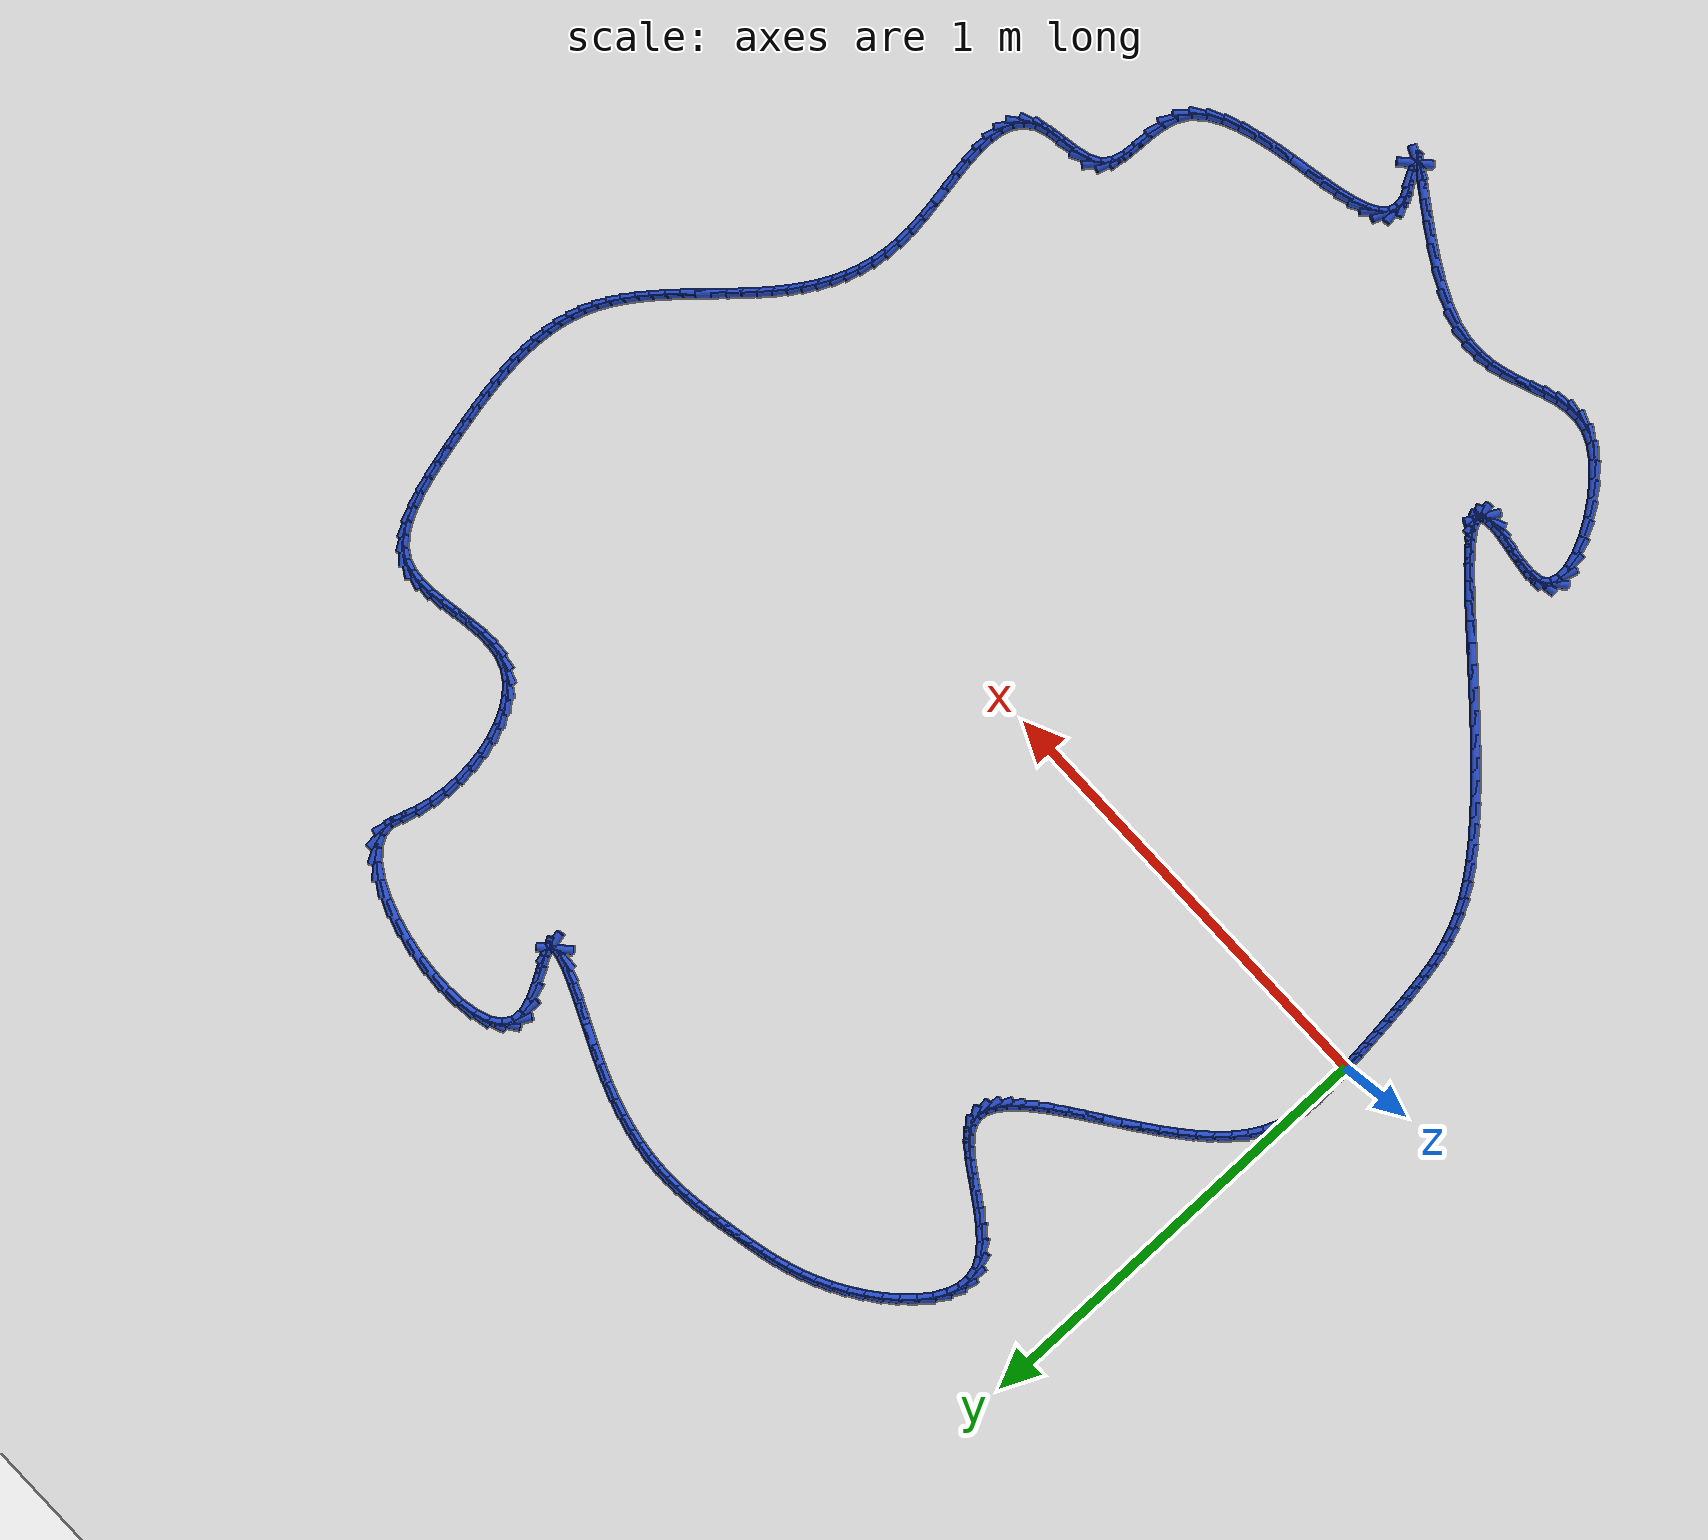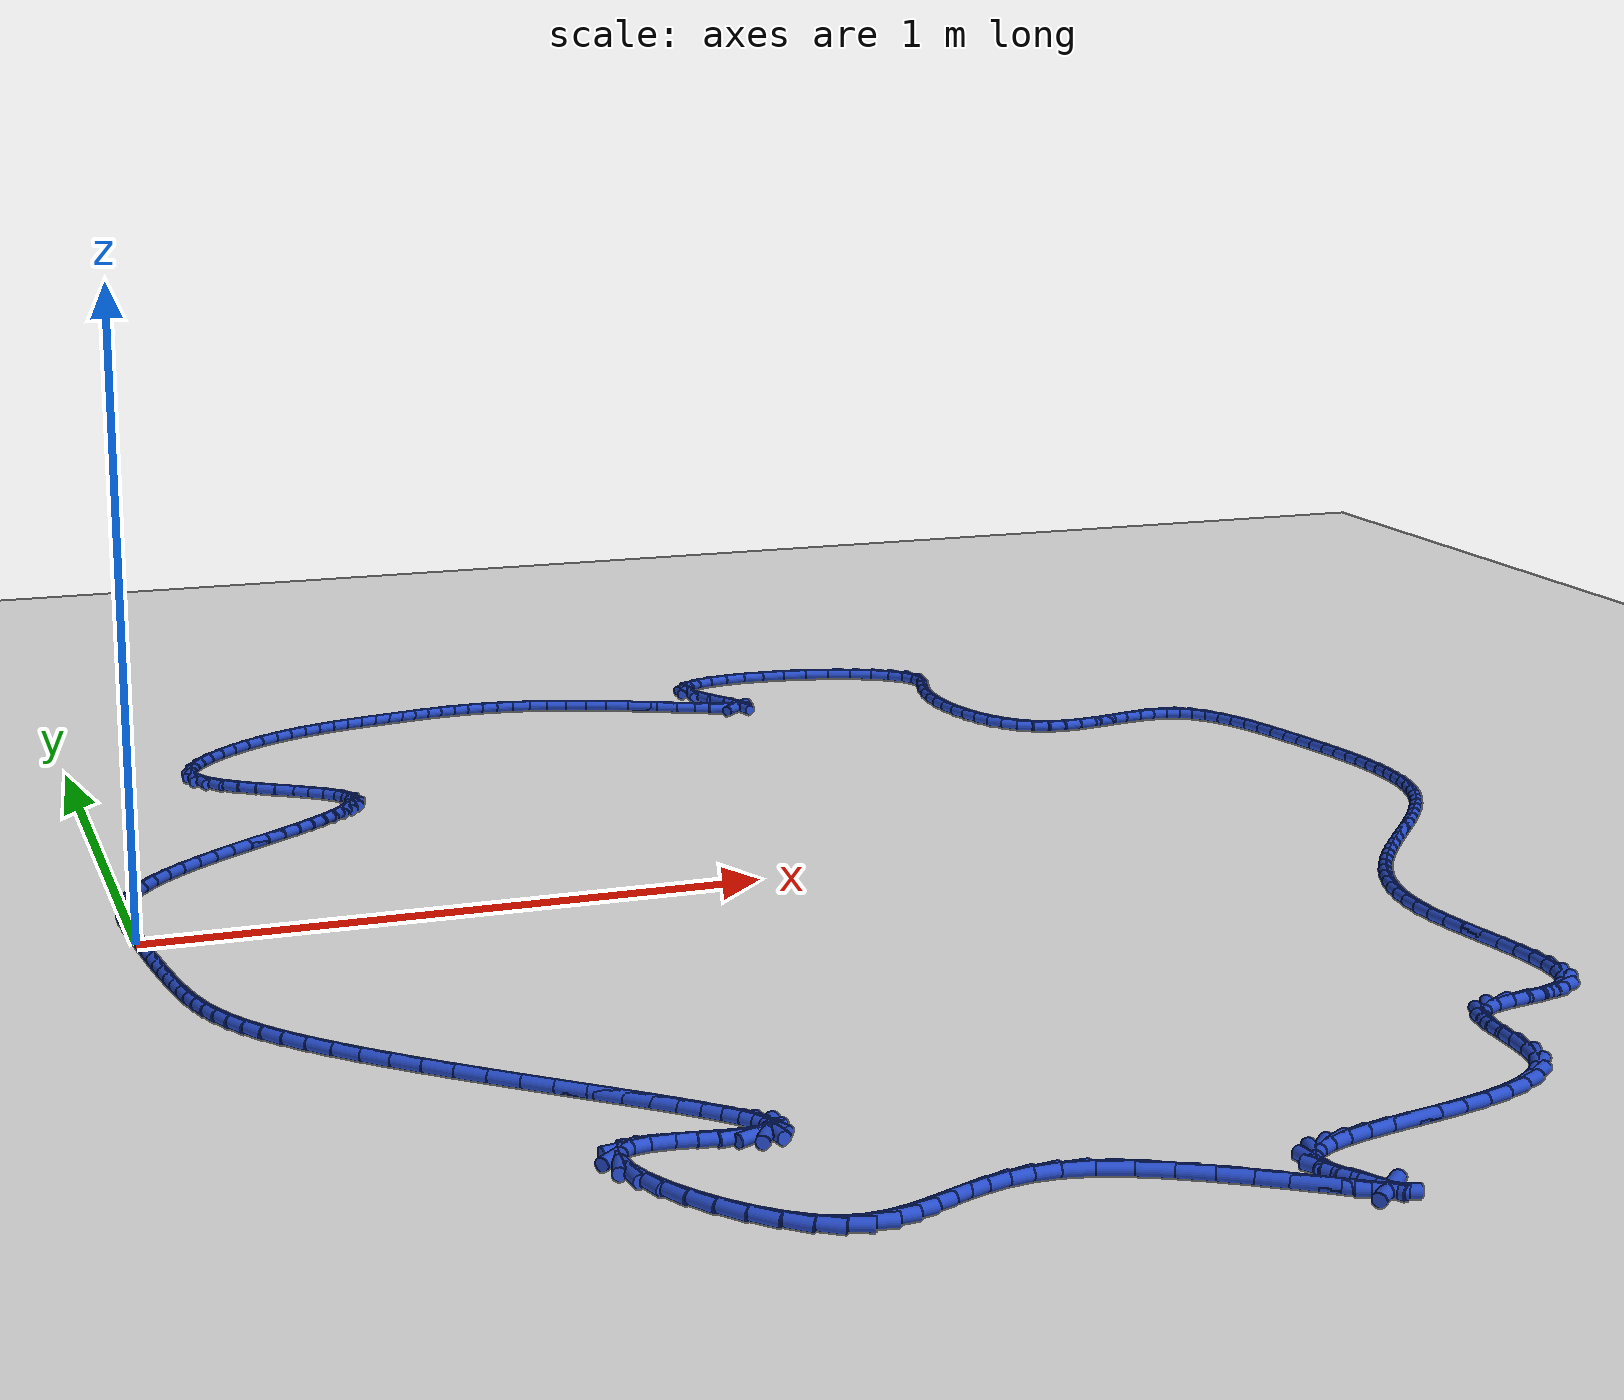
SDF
<sdf version="1.6">
 <world name="default">
  <light name="sun" type="directional">
   <pose>0 0 10 0 -0 0</pose>
   <diffuse>0.8 0.8 0.8 1</diffuse>
   <specular>0.2 0.2 0.2 1</specular>
   <attenuation>
    <range>1000</range>
    <constant>0.9</constant>
    <linear>0.01</linear>
    <quadratic>0.001</quadratic>
   </attenuation>
   <direction>-0.5 0.1 -0.9</direction>
  </light>
  <model name="ground_plane">
   <static>1</static>
   <link name="link">
    <collision name="collision">
     <geometry><plane><normal>0 0 1</normal><size>100 100</size></plane></geometry>
     <surface><friction><ode><mu>100</mu><mu2>50</mu2></ode></friction></surface>
    </collision>
    <visual name="visual">
     <cast_shadows>0</cast_shadows>
     <geometry><plane><normal>0 0 1</normal><size>100 100</size></plane></geometry>
     <material>
      <script><uri>file://media/materials/scripts/gazebo.material</uri><name>Gazebo/WhiteGlow</name></script>
     </material>
    </visual>
   </link>
  </model>
  <gravity>0 0 -9.8</gravity>
  <magnetic_field>6e-06 2.3e-05 -4.2e-05</magnetic_field>
  <atmosphere type="adiabatic"/>
  <physics name="default_physics" default="0" type="ode">
   <max_step_size>0.001</max_step_size>
   <real_time_factor>1</real_time_factor>
   <real_time_update_rate>1000</real_time_update_rate>
  </physics>
  <scene><ambient>0.4 0.4 0.4 1</ambient><background>0.7 0.7 0.7 1</background><shadows>1</shadows></scene>
  <spherical_coordinates>
   <surface_model>EARTH_WGS84</surface_model>
   <latitude_deg>0</latitude_deg>
   <longitude_deg>0</longitude_deg>
   <elevation>0</elevation>
   <heading_deg>0</heading_deg>
  </spherical_coordinates>
  <model name="line">
   <link name="link_0">
    <pose>-2.42861286636753e-17 3.469446951953614e-17 0.01 0 1.57 -1.4951676682161972</pose>
    <collision name="collision">
     <geometry><cylinder><radius>0.01</radius><length>0.08</length></cylinder></geometry>
    </collision>
    <visual name="visual">
     <material>
      <script><name>Gazebo/Blue</name><uri>file://media/materials/scripts/gazebo.material</uri></script>
     </material>
     <geometry><cylinder><radius>0.01</radius><length>0.08</length></cylinder></geometry>
    </visual>
   </link>
   <link name="link_1">
    <pose>-0.0024231983915060803 0.03197963166220904 0.01 0 1.57 -1.520776995941854</pose>
    <collision name="collision">
     <geometry><cylinder><radius>0.01</radius><length>0.08</length></cylinder></geometry>
    </collision>
    <visual name="visual">
     <material>
      <script><name>Gazebo/Blue</name><uri>file://media/materials/scripts/gazebo.material</uri></script>
     </material>
     <geometry><cylinder><radius>0.01</radius><length>0.08</length></cylinder></geometry>
    </visual>
   </link>
   <link name="link_2">
    <pose>-0.004021602005209488 0.06390869450469114 0.01 0 1.57 -1.5667021113652158</pose>
    <collision name="collision">
     <geometry><cylinder><radius>0.01</radius><length>0.08</length></cylinder></geometry>
    </collision>
    <visual name="visual">
     <material>
      <script><name>Gazebo/Blue</name><uri>file://media/materials/scripts/gazebo.material</uri></script>
     </material>
     <geometry><cylinder><radius>0.01</radius><length>0.08</length></cylinder></geometry>
    </visual>
   </link>
   <link name="link_3">
    <pose>-0.0041515814430665285 0.09565561007965417 0.01 0 1.57 1.5078229732911912</pose>
    <collision name="collision">
     <geometry><cylinder><radius>0.01</radius><length>0.08</length></cylinder></geometry>
    </collision>
    <visual name="visual">
     <material>
      <script><name>Gazebo/Blue</name><uri>file://media/materials/scripts/gazebo.material</uri></script>
     </material>
     <geometry><cylinder><radius>0.01</radius><length>0.08</length></cylinder></geometry>
    </visual>
   </link>
   <link name="link_4">
    <pose>-0.002169507307033483 0.12708879993930586 0.01 0 1.57 1.419080571154896</pose>
    <collision name="collision">
     <geometry><cylinder><radius>0.01</radius><length>0.08</length></cylinder></geometry>
    </collision>
    <visual name="visual">
     <material>
      <script><name>Gazebo/Blue</name><uri>file://media/materials/scripts/gazebo.material</uri></script>
     </material>
     <geometry><cylinder><radius>0.01</radius><length>0.08</length></cylinder></geometry>
    </visual>
   </link>
   <link name="link_5">
    <pose>0.0025682498009333594 0.15807668563585411 0.01 0 1.57 1.309350844203637</pose>
    <collision name="collision">
     <geometry><cylinder><radius>0.01</radius><length>0.08</length></cylinder></geometry>
    </collision>
    <visual name="visual">
     <material>
      <script><name>Gazebo/Blue</name><uri>file://media/materials/scripts/gazebo.material</uri></script>
     </material>
     <geometry><cylinder><radius>0.01</radius><length>0.08</length></cylinder></geometry>
    </visual>
   </link>
   <link name="link_6">
    <pose>0.010705319278877728 0.18848768872150673 0.01 0 1.57 1.181642345819273</pose>
    <collision name="collision">
     <geometry><cylinder><radius>0.01</radius><length>0.08</length></cylinder></geometry>
    </collision>
    <visual name="visual">
     <material>
      <script><name>Gazebo/Blue</name><uri>file://media/materials/scripts/gazebo.material</uri></script>
     </material>
     <geometry><cylinder><radius>0.01</radius><length>0.08</length></cylinder></geometry>
    </visual>
   </link>
   <link name="link_7">
    <pose>0.022885330524843324 0.2181902307484714 0.01 0 1.57 1.0456067004906662</pose>
    <collision name="collision">
     <geometry><cylinder><radius>0.01</radius><length>0.08</length></cylinder></geometry>
    </collision>
    <visual name="visual">
     <material>
      <script><name>Gazebo/Blue</name><uri>file://media/materials/scripts/gazebo.material</uri></script>
     </material>
     <geometry><cylinder><radius>0.01</radius><length>0.08</length></cylinder></geometry>
    </visual>
   </link>
   <link name="link_8">
    <pose>0.03962026689619942 0.24706979219742364 0.01 0 1.57 0.9286825390707635</pose>
    <collision name="collision">
     <geometry><cylinder><radius>0.01</radius><length>0.08</length></cylinder></geometry>
    </collision>
    <visual name="visual">
     <material>
      <script><name>Gazebo/Blue</name><uri>file://media/materials/scripts/gazebo.material</uri></script>
     </material>
     <geometry><cylinder><radius>0.01</radius><length>0.08</length></cylinder></geometry>
    </visual>
   </link>
   <link name="link_9">
    <pose>0.060596329189876307 0.2751188599242867 0.01 0 1.57 0.8368329069749436</pose>
    <collision name="collision">
     <geometry><cylinder><radius>0.01</radius><length>0.08</length></cylinder></geometry>
    </collision>
    <visual name="visual">
     <material>
      <script><name>Gazebo/Blue</name><uri>file://media/materials/scripts/gazebo.material</uri></script>
     </material>
     <geometry><cylinder><radius>0.01</radius><length>0.08</length></cylinder></geometry>
    </visual>
   </link>
   <link name="link_10">
    <pose>0.08518024386516361 0.3023713188387736 0.01 0 1.57 0.7656408068478139</pose>
    <collision name="collision">
     <geometry><cylinder><radius>0.01</radius><length>0.08</length></cylinder></geometry>
    </collision>
    <visual name="visual">
     <material>
      <script><name>Gazebo/Blue</name><uri>file://media/materials/scripts/gazebo.material</uri></script>
     </material>
     <geometry><cylinder><radius>0.01</radius><length>0.08</length></cylinder></geometry>
    </visual>
   </link>
   <link name="link_11">
    <pose>0.11273804569964228 0.32886114347994544 0.01 0 1.57 0.7112147203467966</pose>
    <collision name="collision">
     <geometry><cylinder><radius>0.01</radius><length>0.08</length></cylinder></geometry>
    </collision>
    <visual name="visual">
     <material>
      <script><name>Gazebo/Blue</name><uri>file://media/materials/scripts/gazebo.material</uri></script>
     </material>
     <geometry><cylinder><radius>0.01</radius><length>0.08</length></cylinder></geometry>
    </visual>
   </link>
   <link name="link_12">
    <pose>0.1426357694708931 0.35462230838686293 0.01 0 1.57 0.670550532819632</pose>
    <collision name="collision">
     <geometry><cylinder><radius>0.01</radius><length>0.08</length></cylinder></geometry>
    </collision>
    <visual name="visual">
     <material>
      <script><name>Gazebo/Blue</name><uri>file://media/materials/scripts/gazebo.material</uri></script>
     </material>
     <geometry><cylinder><radius>0.01</radius><length>0.08</length></cylinder></geometry>
    </visual>
   </link>
   <link name="link_13">
    <pose>0.17423944995649707 0.3796887880985874 0.01 0 1.57 0.6415202379043854</pose>
    <collision name="collision">
     <geometry><cylinder><radius>0.01</radius><length>0.08</length></cylinder></geometry>
    </collision>
    <visual name="visual">
     <material>
      <script><name>Gazebo/Blue</name><uri>file://media/materials/scripts/gazebo.material</uri></script>
     </material>
     <geometry><cylinder><radius>0.01</radius><length>0.08</length></cylinder></geometry>
    </visual>
   </link>
   <link name="link_14">
    <pose>0.20691512193403513 0.40409455715417963 0.01 0 1.57 0.6227723261044366</pose>
    <collision name="collision">
     <geometry><cylinder><radius>0.01</radius><length>0.08</length></cylinder></geometry>
    </collision>
    <visual name="visual">
     <material>
      <script><name>Gazebo/Blue</name><uri>file://media/materials/scripts/gazebo.material</uri></script>
     </material>
     <geometry><cylinder><radius>0.01</radius><length>0.08</length></cylinder></geometry>
    </visual>
   </link>
   <link name="link_15">
    <pose>0.24002882018108815 0.4278735900927007 0.01 0 1.57 0.6136526146524506</pose>
    <collision name="collision">
     <geometry><cylinder><radius>0.01</radius><length>0.08</length></cylinder></geometry>
    </collision>
    <visual name="visual">
     <material>
      <script><name>Gazebo/Blue</name><uri>file://media/materials/scripts/gazebo.material</uri></script>
     </material>
     <geometry><cylinder><radius>0.01</radius><length>0.08</length></cylinder></geometry>
    </visual>
   </link>
   <link name="link_16">
    <pose>0.2729465794752371 0.45105986145321164 0.01 0 1.57 0.6141892470630065</pose>
    <collision name="collision">
     <geometry><cylinder><radius>0.01</radius><length>0.08</length></cylinder></geometry>
    </collision>
    <visual name="visual">
     <material>
      <script><name>Gazebo/Blue</name><uri>file://media/materials/scripts/gazebo.material</uri></script>
     </material>
     <geometry><cylinder><radius>0.01</radius><length>0.08</length></cylinder></geometry>
    </visual>
   </link>
   <link name="link_17">
    <pose>0.3050344345940627 0.4736873457747733 0.01 0 1.57 0.6251705492804259</pose>
    <collision name="collision">
     <geometry><cylinder><radius>0.01</radius><length>0.08</length></cylinder></geometry>
    </collision>
    <visual name="visual">
     <material>
      <script><name>Gazebo/Blue</name><uri>file://media/materials/scripts/gazebo.material</uri></script>
     </material>
     <geometry><cylinder><radius>0.01</radius><length>0.08</length></cylinder></geometry>
    </visual>
   </link>
   <link name="link_18">
    <pose>0.33565842031514603 0.4957900175964468 0.01 0 1.57 0.6483567855411126</pose>
    <collision name="collision">
     <geometry><cylinder><radius>0.01</radius><length>0.08</length></cylinder></geometry>
    </collision>
    <visual name="visual">
     <material>
      <script><name>Gazebo/Blue</name><uri>file://media/materials/scripts/gazebo.material</uri></script>
     </material>
     <geometry><cylinder><radius>0.01</radius><length>0.08</length></cylinder></geometry>
    </visual>
   </link>
   <link name="link_19">
    <pose>0.3641845714160681 0.5174018514572932 0.01 0 1.57 0.6869011520319974</pose>
    <collision name="collision">
     <geometry><cylinder><radius>0.01</radius><length>0.08</length></cylinder></geometry>
    </collision>
    <visual name="visual">
     <material>
      <script><name>Gazebo/Blue</name><uri>file://media/materials/scripts/gazebo.material</uri></script>
     </material>
     <geometry><cylinder><radius>0.01</radius><length>0.08</length></cylinder></geometry>
    </visual>
   </link>
   <link name="link_20">
    <pose>0.3899789226744096 0.5385568218963733 0.01 0 1.57 0.7461116596463969</pose>
    <collision name="collision">
     <geometry><cylinder><radius>0.01</radius><length>0.08</length></cylinder></geometry>
    </collision>
    <visual name="visual">
     <material>
      <script><name>Gazebo/Blue</name><uri>file://media/materials/scripts/gazebo.material</uri></script>
     </material>
     <geometry><cylinder><radius>0.01</radius><length>0.08</length></cylinder></geometry>
    </visual>
   </link>
   <link name="link_21">
    <pose>0.4124075088677516 0.5592889034527485 0.01 0 1.57 0.8347316232011791</pose>
    <collision name="collision">
     <geometry><cylinder><radius>0.01</radius><length>0.08</length></cylinder></geometry>
    </collision>
    <visual name="visual">
     <material>
      <script><name>Gazebo/Blue</name><uri>file://media/materials/scripts/gazebo.material</uri></script>
     </material>
     <geometry><cylinder><radius>0.01</radius><length>0.08</length></cylinder></geometry>
    </visual>
   </link>
   <link name="link_22">
    <pose>0.430836364773675 0.5796320706654792 0.01 0 1.57 0.9667020699671817</pose>
    <collision name="collision">
     <geometry><cylinder><radius>0.01</radius><length>0.08</length></cylinder></geometry>
    </collision>
    <visual name="visual">
     <material>
      <script><name>Gazebo/Blue</name><uri>file://media/materials/scripts/gazebo.material</uri></script>
     </material>
     <geometry><cylinder><radius>0.01</radius><length>0.08</length></cylinder></geometry>
    </visual>
   </link>
   <link name="link_23">
    <pose>0.44463152516976046 0.5996202980736268 0.01 0 1.57 1.1616736492888196</pose>
    <collision name="collision">
     <geometry><cylinder><radius>0.01</radius><length>0.08</length></cylinder></geometry>
    </collision>
    <visual name="visual">
     <material>
      <script><name>Gazebo/Blue</name><uri>file://media/materials/scripts/gazebo.material</uri></script>
     </material>
     <geometry><cylinder><radius>0.01</radius><length>0.08</length></cylinder></geometry>
    </visual>
   </link>
   <link name="link_24">
    <pose>0.4531590248335893 0.6192875602162522 0.01 0 1.57 1.4361243365622256</pose>
    <collision name="collision">
     <geometry><cylinder><radius>0.01</radius><length>0.08</length></cylinder></geometry>
    </collision>
    <visual name="visual">
     <material>
      <script><name>Gazebo/Blue</name><uri>file://media/materials/scripts/gazebo.material</uri></script>
     </material>
     <geometry><cylinder><radius>0.01</radius><length>0.08</length></cylinder></geometry>
    </visual>
   </link>
   <link name="link_25">
    <pose>0.455784898542742 0.6386678316324162 0.01 0 1.57 -1.369168255120884</pose>
    <collision name="collision">
     <geometry><cylinder><radius>0.01</radius><length>0.08</length></cylinder></geometry>
    </collision>
    <visual name="visual">
     <material>
      <script><name>Gazebo/Blue</name><uri>file://media/materials/scripts/gazebo.material</uri></script>
     </material>
     <geometry><cylinder><radius>0.01</radius><length>0.08</length></cylinder></geometry>
    </visual>
   </link>
   <link name="link_26">
    <pose>0.4518751810747999 0.6577950868611806 0.01 0 1.57 -1.040964239242349</pose>
    <collision name="collision">
     <geometry><cylinder><radius>0.01</radius><length>0.08</length></cylinder></geometry>
    </collision>
    <visual name="visual">
     <material>
      <script><name>Gazebo/Blue</name><uri>file://media/materials/scripts/gazebo.material</uri></script>
     </material>
     <geometry><cylinder><radius>0.01</radius><length>0.08</length></cylinder></geometry>
    </visual>
   </link>
   <link name="link_27">
    <pose>0.4408006305159704 0.6767035923985502 0.01 0 1.57 -0.8018803755980188</pose>
    <collision name="collision">
     <geometry><cylinder><radius>0.01</radius><length>0.08</length></cylinder></geometry>
    </collision>
    <visual name="visual">
     <material>
      <script><name>Gazebo/Blue</name><uri>file://media/materials/scripts/gazebo.material</uri></script>
     </material>
     <geometry><cylinder><radius>0.01</radius><length>0.08</length></cylinder></geometry>
    </visual>
   </link>
   <link name="link_28">
    <pose>0.4226414506183319 0.6954714669648075 0.01 0 1.57 -0.6704025739768827</pose>
    <collision name="collision">
     <geometry><cylinder><radius>0.01</radius><length>0.08</length></cylinder></geometry>
    </collision>
    <visual name="visual">
     <material>
      <script><name>Gazebo/Blue</name><uri>file://media/materials/scripts/gazebo.material</uri></script>
     </material>
     <geometry><cylinder><radius>0.01</radius><length>0.08</length></cylinder></geometry>
    </visual>
   </link>
   <link name="link_29">
    <pose>0.39893692029679473 0.7142670175699848 0.01 0 1.57 -0.6041358656267266</pose>
    <collision name="collision">
     <geometry><cylinder><radius>0.01</radius><length>0.08</length></cylinder></geometry>
    </collision>
    <visual name="visual">
     <material>
      <script><name>Gazebo/Blue</name><uri>file://media/materials/scripts/gazebo.material</uri></script>
     </material>
     <geometry><cylinder><radius>0.01</radius><length>0.08</length></cylinder></geometry>
    </visual>
   </link>
   <link name="link_30">
    <pose>0.37140587851153106 0.7332696501817295 0.01 0 1.57 -0.5793096695045861</pose>
    <collision name="collision">
     <geometry><cylinder><radius>0.01</radius><length>0.08</length></cylinder></geometry>
    </collision>
    <visual name="visual">
     <material>
      <script><name>Gazebo/Blue</name><uri>file://media/materials/scripts/gazebo.material</uri></script>
     </material>
     <geometry><cylinder><radius>0.01</radius><length>0.08</length></cylinder></geometry>
    </visual>
   </link>
   <link name="link_31">
    <pose>0.34176716422271297 0.7526587707676894 0.01 0 1.57 -0.5865405830983392</pose>
    <collision name="collision">
     <geometry><cylinder><radius>0.01</radius><length>0.08</length></cylinder></geometry>
    </collision>
    <visual name="visual">
     <material>
      <script><name>Gazebo/Blue</name><uri>file://media/materials/scripts/gazebo.material</uri></script>
     </material>
     <geometry><cylinder><radius>0.01</radius><length>0.08</length></cylinder></geometry>
    </visual>
   </link>
   <link name="link_32">
    <pose>0.31173961639051234 0.772613785295512 0.01 0 1.57 -0.6248965012241878</pose>
    <collision name="collision">
     <geometry><cylinder><radius>0.01</radius><length>0.08</length></cylinder></geometry>
    </collision>
    <visual name="visual">
     <material>
      <script><name>Gazebo/Blue</name><uri>file://media/materials/scripts/gazebo.material</uri></script>
     </material>
     <geometry><cylinder><radius>0.01</radius><length>0.08</length></cylinder></geometry>
    </visual>
   </link>
   <link name="link_33">
    <pose>0.28304207397510156 0.7933140997328448 0.01 0 1.57 -0.7004883360157022</pose>
    <collision name="collision">
     <geometry><cylinder><radius>0.01</radius><length>0.08</length></cylinder></geometry>
    </collision>
    <visual name="visual">
     <material>
      <script><name>Gazebo/Blue</name><uri>file://media/materials/scripts/gazebo.material</uri></script>
     </material>
     <geometry><cylinder><radius>0.01</radius><length>0.08</length></cylinder></geometry>
    </visual>
   </link>
   <link name="link_34">
    <pose>0.25739337593665257 0.8149391200473355 0.01 0 1.57 -0.8277509742001534</pose>
    <collision name="collision">
     <geometry><cylinder><radius>0.01</radius><length>0.08</length></cylinder></geometry>
    </collision>
    <visual name="visual">
     <material>
      <script><name>Gazebo/Blue</name><uri>file://media/materials/scripts/gazebo.material</uri></script>
     </material>
     <geometry><cylinder><radius>0.01</radius><length>0.08</length></cylinder></geometry>
    </visual>
   </link>
   <link name="link_35">
    <pose>0.23651236123533753 0.8376682522066319 0.01 0 1.57 -1.0307779855114736</pose>
    <collision name="collision">
     <geometry><cylinder><radius>0.01</radius><length>0.08</length></cylinder></geometry>
    </collision>
    <visual name="visual">
     <material>
      <script><name>Gazebo/Blue</name><uri>file://media/materials/scripts/gazebo.material</uri></script>
     </material>
     <geometry><cylinder><radius>0.01</radius><length>0.08</length></cylinder></geometry>
    </visual>
   </link>
   <link name="link_36">
    <pose>0.22211786883132853 0.8616809021783809 0.01 0 1.57 -1.3268220585196373</pose>
    <collision name="collision">
     <geometry><cylinder><radius>0.01</radius><length>0.08</length></cylinder></geometry>
    </collision>
    <visual name="visual">
     <material>
      <script><name>Gazebo/Blue</name><uri>file://media/materials/scripts/gazebo.material</uri></script>
     </material>
     <geometry><cylinder><radius>0.01</radius><length>0.08</length></cylinder></geometry>
    </visual>
   </link>
   <link name="link_37">
    <pose>0.2157850015590055 0.887120939372997 0.01 0 1.57 1.5058635755369905</pose>
    <collision name="collision">
     <geometry><cylinder><radius>0.01</radius><length>0.08</length></cylinder></geometry>
    </collision>
    <visual name="visual">
     <material>
      <script><name>Gazebo/Blue</name><uri>file://media/materials/scripts/gazebo.material</uri></script>
     </material>
     <geometry><cylinder><radius>0.01</radius><length>0.08</length></cylinder></geometry>
    </visual>
   </link>
   <link name="link_38">
    <pose>0.21751610432186064 0.9137433928733975 0.01 0 1.57 1.2582718332801102</pose>
    <collision name="collision">
     <geometry><cylinder><radius>0.01</radius><length>0.08</length></cylinder></geometry>
    </collision>
    <visual name="visual">
     <material>
      <script><name>Gazebo/Blue</name><uri>file://media/materials/scripts/gazebo.material</uri></script>
     </material>
     <geometry><cylinder><radius>0.01</radius><length>0.08</length></cylinder></geometry>
    </visual>
   </link>
   <link name="link_39">
    <pose>0.22634359132044546 0.9410634912409002 0.01 0 1.57 1.0735248415382026</pose>
    <collision name="collision">
     <geometry><cylinder><radius>0.01</radius><length>0.08</length></cylinder></geometry>
    </collision>
    <visual name="visual">
     <material>
      <script><name>Gazebo/Blue</name><uri>file://media/materials/scripts/gazebo.material</uri></script>
     </material>
     <geometry><cylinder><radius>0.01</radius><length>0.08</length></cylinder></geometry>
    </visual>
   </link>
   <link name="link_40">
    <pose>0.24128560792490975 0.968592935286887 0.01 0 1.57 0.9358794147932371</pose>
    <collision name="collision">
     <geometry><cylinder><radius>0.01</radius><length>0.08</length></cylinder></geometry>
    </collision>
    <visual name="visual">
     <material>
      <script><name>Gazebo/Blue</name><uri>file://media/materials/scripts/gazebo.material</uri></script>
     </material>
     <geometry><cylinder><radius>0.01</radius><length>0.08</length></cylinder></geometry>
    </visual>
   </link>
   <link name="link_41">
    <pose>0.26136029950540357 0.9958434258227414 0.01 0 1.57 0.8298921775060079</pose>
    <collision name="collision">
     <geometry><cylinder><radius>0.01</radius><length>0.08</length></cylinder></geometry>
    </collision>
    <visual name="visual">
     <material>
      <script><name>Gazebo/Blue</name><uri>file://media/materials/scripts/gazebo.material</uri></script>
     </material>
     <geometry><cylinder><radius>0.01</radius><length>0.08</length></cylinder></geometry>
    </visual>
   </link>
   <link name="link_42">
    <pose>0.28558581143207684 1.0223266636598471 0.01 0 1.57 0.7442450029475504</pose>
    <collision name="collision">
     <geometry><cylinder><radius>0.01</radius><length>0.08</length></cylinder></geometry>
    </collision>
    <visual name="visual">
     <material>
      <script><name>Gazebo/Blue</name><uri>file://media/materials/scripts/gazebo.material</uri></script>
     </material>
     <geometry><cylinder><radius>0.01</radius><length>0.08</length></cylinder></geometry>
    </visual>
   </link>
   <link name="link_43">
    <pose>0.31298028907507935 1.0475543496095863 0.01 0 1.57 0.6709898506800154</pose>
    <collision name="collision">
     <geometry><cylinder><radius>0.01</radius><length>0.08</length></cylinder></geometry>
    </collision>
    <visual name="visual">
     <material>
      <script><name>Gazebo/Blue</name><uri>file://media/materials/scripts/gazebo.material</uri></script>
     </material>
     <geometry><cylinder><radius>0.01</radius><length>0.08</length></cylinder></geometry>
    </visual>
   </link>
   <link name="link_44">
    <pose>0.3425618778045614 1.0710381844833428 0.01 0 1.57 0.6041757468511973</pose>
    <collision name="collision">
     <geometry><cylinder><radius>0.01</radius><length>0.08</length></cylinder></geometry>
    </collision>
    <visual name="visual">
     <material>
      <script><name>Gazebo/Blue</name><uri>file://media/materials/scripts/gazebo.material</uri></script>
     </material>
     <geometry><cylinder><radius>0.01</radius><length>0.08</length></cylinder></geometry>
    </visual>
   </link>
   <link name="link_45">
    <pose>0.3733487229906724 1.092289869092499 0.01 0 1.57 0.5387756803722319</pose>
    <collision name="collision">
     <geometry><cylinder><radius>0.01</radius><length>0.08</length></cylinder></geometry>
    </collision>
    <visual name="visual">
     <material>
      <script><name>Gazebo/Blue</name><uri>file://media/materials/scripts/gazebo.material</uri></script>
     </material>
     <geometry><cylinder><radius>0.01</radius><length>0.08</length></cylinder></geometry>
    </visual>
   </link>
   <link name="link_46">
    <pose>0.4043806218387051 1.11083970193548 0.01 0 1.57 0.47365859813722133</pose>
    <collision name="collision">
     <geometry><cylinder><radius>0.01</radius><length>0.08</length></cylinder></geometry>
    </collision>
    <visual name="visual">
     <material>
      <script><name>Gazebo/Blue</name><uri>file://media/materials/scripts/gazebo.material</uri></script>
     </material>
     <geometry><cylinder><radius>0.01</radius><length>0.08</length></cylinder></geometry>
    </visual>
   </link>
   <link name="link_47">
    <pose>0.43516333120259965 1.126618214177498 0.01 0 1.57 0.4119890173657231</pose>
    <collision name="collision">
     <geometry><cylinder><radius>0.01</radius><length>0.08</length></cylinder></geometry>
    </collision>
    <visual name="visual">
     <material>
      <script><name>Gazebo/Blue</name><uri>file://media/materials/scripts/gazebo.material</uri></script>
     </material>
     <geometry><cylinder><radius>0.01</radius><length>0.08</length></cylinder></geometry>
    </visual>
   </link>
   <link name="link_48">
    <pose>0.46565143730910025 1.1399414557241312 0.01 0 1.57 0.35549149577950834</pose>
    <collision name="collision">
     <geometry><cylinder><radius>0.01</radius><length>0.08</length></cylinder></geometry>
    </collision>
    <visual name="visual">
     <material>
      <script><name>Gazebo/Blue</name><uri>file://media/materials/scripts/gazebo.material</uri></script>
     </material>
     <geometry><cylinder><radius>0.01</radius><length>0.08</length></cylinder></geometry>
    </visual>
   </link>
   <link name="link_49">
    <pose>0.49581775065805883 1.1511411300884065 0.01 0 1.57 0.3056291293573806</pose>
    <collision name="collision">
     <geometry><cylinder><radius>0.01</radius><length>0.08</length></cylinder></geometry>
    </collision>
    <visual name="visual">
     <material>
      <script><name>Gazebo/Blue</name><uri>file://media/materials/scripts/gazebo.material</uri></script>
     </material>
     <geometry><cylinder><radius>0.01</radius><length>0.08</length></cylinder></geometry>
    </visual>
   </link>
   <link name="link_50">
    <pose>0.5256350817493278 1.16054894078335 0.01 0 1.57 0.2636655343947881</pose>
    <collision name="collision">
     <geometry><cylinder><radius>0.01</radius><length>0.08</length></cylinder></geometry>
    </collision>
    <visual name="visual">
     <material>
      <script><name>Gazebo/Blue</name><uri>file://media/materials/scripts/gazebo.material</uri></script>
     </material>
     <geometry><cylinder><radius>0.01</radius><length>0.08</length></cylinder></geometry>
    </visual>
   </link>
   <link name="link_51">
    <pose>0.5550762410827587 1.1684965913219874 0.01 0 1.57 0.23065893804282758</pose>
    <collision name="collision">
     <geometry><cylinder><radius>0.01</radius><length>0.08</length></cylinder></geometry>
    </collision>
    <visual name="visual">
     <material>
      <script><name>Gazebo/Blue</name><uri>file://media/materials/scripts/gazebo.material</uri></script>
     </material>
     <geometry><cylinder><radius>0.01</radius><length>0.08</length></cylinder></geometry>
    </visual>
   </link>
   <link name="link_52">
    <pose>0.5841140391582038 1.175315785217346 0.01 0 1.57 0.20749162001211907</pose>
    <collision name="collision">
     <geometry><cylinder><radius>0.01</radius><length>0.08</length></cylinder></geometry>
    </collision>
    <visual name="visual">
     <material>
      <script><name>Gazebo/Blue</name><uri>file://media/materials/scripts/gazebo.material</uri></script>
     </material>
     <geometry><cylinder><radius>0.01</radius><length>0.08</length></cylinder></geometry>
    </visual>
   </link>
   <link name="link_53">
    <pose>0.6127212864755149 1.1813382259824512 0.01 0 1.57 0.19491457491919117</pose>
    <collision name="collision">
     <geometry><cylinder><radius>0.01</radius><length>0.08</length></cylinder></geometry>
    </collision>
    <visual name="visual">
     <material>
      <script><name>Gazebo/Blue</name><uri>file://media/materials/scripts/gazebo.material</uri></script>
     </material>
     <geometry><cylinder><radius>0.01</radius><length>0.08</length></cylinder></geometry>
    </visual>
   </link>
   <link name="link_54">
    <pose>0.6408708285580935 1.186895538138761 0.01 0 1.57 0.18910720785775761</pose>
    <collision name="collision">
     <geometry><cylinder><radius>0.01</radius><length>0.08</length></cylinder></geometry>
    </collision>
    <visual name="visual">
     <material>
      <script><name>Gazebo/Blue</name><uri>file://media/materials/scripts/gazebo.material</uri></script>
     </material>
     <geometry><cylinder><radius>0.01</radius><length>0.08</length></cylinder></geometry>
    </visual>
   </link>
   <link name="link_55">
    <pose>0.6685882123869992 1.1922004841569647 0.01 0 1.57 0.1767876970871028</pose>
    <collision name="collision">
     <geometry><cylinder><radius>0.01</radius><length>0.08</length></cylinder></geometry>
    </collision>
    <visual name="visual">
     <material>
      <script><name>Gazebo/Blue</name><uri>file://media/materials/scripts/gazebo.material</uri></script>
     </material>
     <geometry><cylinder><radius>0.01</radius><length>0.08</length></cylinder></geometry>
    </visual>
   </link>
   <link name="link_56">
    <pose>0.6960576500471306 1.1971079756917575 0.01 0 1.57 0.15539127253815693</pose>
    <collision name="collision">
     <geometry><cylinder><radius>0.01</radius><length>0.08</length></cylinder></geometry>
    </collision>
    <visual name="visual">
     <material>
      <script><name>Gazebo/Blue</name><uri>file://media/materials/scripts/gazebo.material</uri></script>
     </material>
     <geometry><cylinder><radius>0.01</radius><length>0.08</length></cylinder></geometry>
    </visual>
   </link>
   <link name="link_57">
    <pose>0.7234930921494731 1.2014058525870246 0.01 0 1.57 0.12521693846274587</pose>
    <collision name="collision">
     <geometry><cylinder><radius>0.01</radius><length>0.08</length></cylinder></geometry>
    </collision>
    <visual name="visual">
     <material>
      <script><name>Gazebo/Blue</name><uri>file://media/materials/scripts/gazebo.material</uri></script>
     </material>
     <geometry><cylinder><radius>0.01</radius><length>0.08</length></cylinder></geometry>
    </visual>
   </link>
   <link name="link_58">
    <pose>0.7511084893050125 1.2048819546866523 0.01 0 1.57 0.08697133691234682</pose>
    <collision name="collision">
     <geometry><cylinder><radius>0.01</radius><length>0.08</length></cylinder></geometry>
    </collision>
    <visual name="visual">
     <material>
      <script><name>Gazebo/Blue</name><uri>file://media/materials/scripts/gazebo.material</uri></script>
     </material>
     <geometry><cylinder><radius>0.01</radius><length>0.08</length></cylinder></geometry>
    </visual>
   </link>
   <link name="link_59">
    <pose>0.7791177921247345 1.2073241218345265 0.01 0 1.57 0.04177131289076687</pose>
    <collision name="collision">
     <geometry><cylinder><radius>0.01</radius><length>0.08</length></cylinder></geometry>
    </collision>
    <visual name="visual">
     <material>
      <script><name>Gazebo/Blue</name><uri>file://media/materials/scripts/gazebo.material</uri></script>
     </material>
     <geometry><cylinder><radius>0.01</radius><length>0.08</length></cylinder></geometry>
    </visual>
   </link>
   <link name="link_60">
    <pose>0.8077349512196238 1.2085201938745327 0.01 0 1.57 -0.008905757513272314</pose>
    <collision name="collision">
     <geometry><cylinder><radius>0.01</radius><length>0.08</length></cylinder></geometry>
    </collision>
    <visual name="visual">
     <material>
      <script><name>Gazebo/Blue</name><uri>file://media/materials/scripts/gazebo.material</uri></script>
     </material>
     <geometry><cylinder><radius>0.01</radius><length>0.08</length></cylinder></geometry>
    </visual>
   </link>
   <link name="link_61">
    <pose>0.837173917200667 1.208258010650557 0.01 0 1.57 -0.06333163733935887</pose>
    <collision name="collision">
     <geometry><cylinder><radius>0.01</radius><length>0.08</length></cylinder></geometry>
    </collision>
    <visual name="visual">
     <material>
      <script><name>Gazebo/Blue</name><uri>file://media/materials/scripts/gazebo.material</uri></script>
     </material>
     <geometry><cylinder><radius>0.01</radius><length>0.08</length></cylinder></geometry>
    </visual>
   </link>
   <link name="link_62">
    <pose>0.8676486406788484 1.2063254120064846 0.01 0 1.57 -0.11968504326022786</pose>
    <collision name="collision">
     <geometry><cylinder><radius>0.01</radius><length>0.08</length></cylinder></geometry>
    </collision>
    <visual name="visual">
     <material>
      <script><name>Gazebo/Blue</name><uri>file://media/materials/scripts/gazebo.material</uri></script>
     </material>
     <geometry><cylinder><radius>0.01</radius><length>0.08</length></cylinder></geometry>
    </visual>
   </link>
   <link name="link_63">
    <pose>0.8993730722651547 1.2025102377862014 0.01 0 1.57 -0.17622599723135676</pose>
    <collision name="collision">
     <geometry><cylinder><radius>0.01</radius><length>0.08</length></cylinder></geometry>
    </collision>
    <visual name="visual">
     <material>
      <script><name>Gazebo/Blue</name><uri>file://media/materials/scripts/gazebo.material</uri></script>
     </material>
     <geometry><cylinder><radius>0.01</radius><length>0.08</length></cylinder></geometry>
    </visual>
   </link>
   <link name="link_64">
    <pose>0.9325611625705703 1.1966003278335937 0.01 0 1.57 -0.23144697538883593</pose>
    <collision name="collision">
     <geometry><cylinder><radius>0.01</radius><length>0.08</length></cylinder></geometry>
    </collision>
    <visual name="visual">
     <material>
      <script><name>Gazebo/Blue</name><uri>file://media/materials/scripts/gazebo.material</uri></script>
     </material>
     <geometry><cylinder><radius>0.01</radius><length>0.08</length></cylinder></geometry>
    </visual>
   </link>
   <link name="link_65">
    <pose>0.9674268622060811 1.188383521992547 0.01 0 1.57 -0.284170019272757</pose>
    <collision name="collision">
     <geometry><cylinder><radius>0.01</radius><length>0.08</length></cylinder></geometry>
    </collision>
    <visual name="visual">
     <material>
      <script><name>Gazebo/Blue</name><uri>file://media/materials/scripts/gazebo.material</uri></script>
     </material>
     <geometry><cylinder><radius>0.01</radius><length>0.08</length></cylinder></geometry>
    </visual>
   </link>
   <link name="link_66">
    <pose>1.0041841217826732 1.1776476601069468 0.01 0 1.57 -0.33357930208601577</pose>
    <collision name="collision">
     <geometry><cylinder><radius>0.01</radius><length>0.08</length></cylinder></geometry>
    </collision>
    <visual name="visual">
     <material>
      <script><name>Gazebo/Blue</name><uri>file://media/materials/scripts/gazebo.material</uri></script>
     </material>
     <geometry><cylinder><radius>0.01</radius><length>0.08</length></cylinder></geometry>
    </visual>
   </link>
   <link name="link_67">
    <pose>1.0430468919113314 1.1641805820206792 0.01 0 1.57 -0.3787149812527351</pose>
    <collision name="collision">
     <geometry><cylinder><radius>0.01</radius><length>0.08</length></cylinder></geometry>
    </collision>
    <visual name="visual">
     <material>
      <script><name>Gazebo/Blue</name><uri>file://media/materials/scripts/gazebo.material</uri></script>
     </material>
     <geometry><cylinder><radius>0.01</radius><length>0.08</length></cylinder></geometry>
    </visual>
   </link>
   <link name="link_68">
    <pose>1.0841842123855288 1.1478110768534633 0.01 0 1.57 -0.41126324615828164</pose>
    <collision name="collision">
     <geometry><cylinder><radius>0.01</radius><length>0.08</length></cylinder></geometry>
    </collision>
    <visual name="visual">
     <material>
      <script><name>Gazebo/Blue</name><uri>file://media/materials/scripts/gazebo.material</uri></script>
     </material>
     <geometry><cylinder><radius>0.01</radius><length>0.08</length></cylinder></geometry>
    </visual>
   </link>
   <link name="link_69">
    <pose>1.1268484326085306 1.1292037637036618 0.01 0 1.57 -0.4274422393446067</pose>
    <collision name="collision">
     <geometry><cylinder><radius>0.01</radius><length>0.08</length></cylinder></geometry>
    </collision>
    <visual name="visual">
     <material>
      <script><name>Gazebo/Blue</name><uri>file://media/materials/scripts/gazebo.material</uri></script>
     </material>
     <geometry><cylinder><radius>0.01</radius><length>0.08</length></cylinder></geometry>
    </visual>
   </link>
   <link name="link_70">
    <pose>1.1694354945998873 1.1098041261500406 0.01 0 1.57 -0.42942003754167546</pose>
    <collision name="collision">
     <geometry><cylinder><radius>0.01</radius><length>0.08</length></cylinder></geometry>
    </collision>
    <visual name="visual">
     <material>
      <script><name>Gazebo/Blue</name><uri>file://media/materials/scripts/gazebo.material</uri></script>
     </material>
     <geometry><cylinder><radius>0.01</radius><length>0.08</length></cylinder></geometry>
    </visual>
   </link>
   <link name="link_71">
    <pose>1.2103085036542227 1.091087587999155 0.01 0 1.57 -0.41558499335434157</pose>
    <collision name="collision">
     <geometry><cylinder><radius>0.01</radius><length>0.08</length></cylinder></geometry>
    </collision>
    <visual name="visual">
     <material>
      <script><name>Gazebo/Blue</name><uri>file://media/materials/scripts/gazebo.material</uri></script>
     </material>
     <geometry><cylinder><radius>0.01</radius><length>0.08</length></cylinder></geometry>
    </visual>
   </link>
   <link name="link_72">
    <pose>1.2478305650661614 1.0745295730575588 0.01 0 1.57 -0.37812944372000823</pose>
    <collision name="collision">
     <geometry><cylinder><radius>0.01</radius><length>0.08</length></cylinder></geometry>
    </collision>
    <visual name="visual">
     <material>
      <script><name>Gazebo/Blue</name><uri>file://media/materials/scripts/gazebo.material</uri></script>
     </material>
     <geometry><cylinder><radius>0.01</radius><length>0.08</length></cylinder></geometry>
    </visual>
   </link>
   <link name="link_73">
    <pose>1.2803647841303274 1.0616055051318056 0.01 0 1.57 -0.2929380937873325</pose>
    <collision name="collision">
     <geometry><cylinder><radius>0.01</radius><length>0.08</length></cylinder></geometry>
    </collision>
    <visual name="visual">
     <material>
      <script><name>Gazebo/Blue</name><uri>file://media/materials/scripts/gazebo.material</uri></script>
     </material>
     <geometry><cylinder><radius>0.01</radius><length>0.08</length></cylinder></geometry>
    </visual>
   </link>
   <link name="link_74">
    <pose>1.3062742661413442 1.0537908080284506 0.01 0 1.57 -0.06957884811726305</pose>
    <collision name="collision">
     <geometry><cylinder><radius>0.01</radius><length>0.08</length></cylinder></geometry>
    </collision>
    <visual name="visual">
     <material>
      <script><name>Gazebo/Blue</name><uri>file://media/materials/scripts/gazebo.material</uri></script>
     </material>
     <geometry><cylinder><radius>0.01</radius><length>0.08</length></cylinder></geometry>
    </visual>
   </link>
   <link name="link_75">
    <pose>1.323922116393836 1.0525609055540477 0.01 0 1.57 0.7224478031468782</pose>
    <collision name="collision">
     <geometry><cylinder><radius>0.01</radius><length>0.08</length></cylinder></geometry>
    </collision>
    <visual name="visual">
     <material>
      <script><name>Gazebo/Blue</name><uri>file://media/materials/scripts/gazebo.material</uri></script>
     </material>
     <geometry><cylinder><radius>0.01</radius><length>0.08</length></cylinder></geometry>
    </visual>
   </link>
   <link name="link_76">
    <pose>1.3316714401824277 1.0593912215151517 0.01 0 1.57 -1.3496120685410957</pose>
    <collision name="collision">
     <geometry><cylinder><radius>0.01</radius><length>0.08</length></cylinder></geometry>
    </collision>
    <visual name="visual">
     <material>
      <script><name>Gazebo/Blue</name><uri>file://media/materials/scripts/gazebo.material</uri></script>
     </material>
     <geometry><cylinder><radius>0.01</radius><length>0.08</length></cylinder></geometry>
    </visual>
   </link>
   <link name="link_77">
    <pose>1.3280105312774348 1.0756718242429102 0.01 0 1.57 -1.0800611763445116</pose>
    <collision name="collision">
     <geometry><cylinder><radius>0.01</radius><length>0.08</length></cylinder></geometry>
    </collision>
    <visual name="visual">
     <material>
      <script><name>Gazebo/Blue</name><uri>file://media/materials/scripts/gazebo.material</uri></script>
     </material>
     <geometry><cylinder><radius>0.01</radius><length>0.08</length></cylinder></geometry>
    </visual>
   </link>
   <link name="link_78">
    <pose>1.3147174181506907 1.100549789110419 0.01 0 1.57 -1.043010074607003</pose>
    <collision name="collision">
     <geometry><cylinder><radius>0.01</radius><length>0.08</length></cylinder></geometry>
    </collision>
    <visual name="visual">
     <material>
      <script><name>Gazebo/Blue</name><uri>file://media/materials/scripts/gazebo.material</uri></script>
     </material>
     <geometry><cylinder><radius>0.01</radius><length>0.08</length></cylinder></geometry>
    </visual>
   </link>
   <link name="link_79">
    <pose>1.2971054329115812 1.1307617657625344 0.01 0 1.57 -1.0982033194459906</pose>
    <collision name="collision">
     <geometry><cylinder><radius>0.01</radius><length>0.08</length></cylinder></geometry>
    </collision>
    <visual name="visual">
     <material>
      <script><name>Gazebo/Blue</name><uri>file://media/materials/scripts/gazebo.material</uri></script>
     </material>
     <geometry><cylinder><radius>0.01</radius><length>0.08</length></cylinder></geometry>
    </visual>
   </link>
   <link name="link_80">
    <pose>1.2806622897430027 1.1629255073985398 0.01 0 1.57 -1.262512435571746</pose>
    <collision name="collision">
     <geometry><cylinder><radius>0.01</radius><length>0.08</length></cylinder></geometry>
    </collision>
    <visual name="visual">
     <material>
      <script><name>Gazebo/Blue</name><uri>file://media/materials/scripts/gazebo.material</uri></script>
     </material>
     <geometry><cylinder><radius>0.01</radius><length>0.08</length></cylinder></geometry>
    </visual>
   </link>
   <link name="link_81">
    <pose>1.2708757028278495 1.1936587672177172 0.01 0 1.57 1.5128051599179193</pose>
    <collision name="collision">
     <geometry><cylinder><radius>0.01</radius><length>0.08</length></cylinder></geometry>
    </collision>
    <visual name="visual">
     <material>
      <script><name>Gazebo/Blue</name><uri>file://media/materials/scripts/gazebo.material</uri></script>
     </material>
     <geometry><cylinder><radius>0.01</radius><length>0.08</length></cylinder></geometry>
    </visual>
   </link>
   <link name="link_82">
    <pose>1.2724048519938926 1.2199978581546755 0.01 0 1.57 1.0283300394341726</pose>
    <collision name="collision">
     <geometry><cylinder><radius>0.01</radius><length>0.08</length></cylinder></geometry>
    </collision>
    <visual name="visual">
     <material>
      <script><name>Gazebo/Blue</name><uri>file://media/materials/scripts/gazebo.material</uri></script>
     </material>
     <geometry><cylinder><radius>0.01</radius><length>0.08</length></cylinder></geometry>
    </visual>
   </link>
   <link name="link_83">
    <pose>1.2852616609815208 1.2413267981798968 0.01 0 1.57 0.6317180641579971</pose>
    <collision name="collision">
     <geometry><cylinder><radius>0.01</radius><length>0.08</length></cylinder></geometry>
    </collision>
    <visual name="visual">
     <material>
      <script><name>Gazebo/Blue</name><uri>file://media/materials/scripts/gazebo.material</uri></script>
     </material>
     <geometry><cylinder><radius>0.01</radius><length>0.08</length></cylinder></geometry>
    </visual>
   </link>
   <link name="link_84">
    <pose>1.3078388116097375 1.2578476153630838 0.01 0 1.57 0.37035723255610814</pose>
    <collision name="collision">
     <geometry><cylinder><radius>0.01</radius><length>0.08</length></cylinder></geometry>
    </collision>
    <visual name="visual">
     <material>
      <script><name>Gazebo/Blue</name><uri>file://media/materials/scripts/gazebo.material</uri></script>
     </material>
     <geometry><cylinder><radius>0.01</radius><length>0.08</length></cylinder></geometry>
    </visual>
   </link>
   <link name="link_85">
    <pose>1.338527329039117 1.2697631746861422 0.01 0 1.57 0.19933346647590364</pose>
    <collision name="collision">
     <geometry><cylinder><radius>0.01</radius><length>0.08</length></cylinder></geometry>
    </collision>
    <visual name="visual">
     <material>
      <script><name>Gazebo/Blue</name><uri>file://media/materials/scripts/gazebo.material</uri></script>
     </material>
     <geometry><cylinder><radius>0.01</radius><length>0.08</length></cylinder></geometry>
    </visual>
   </link>
   <link name="link_86">
    <pose>1.3757182384302349 1.2772763411309775 0.01 0 1.57 0.07857595324308744</pose>
    <collision name="collision">
     <geometry><cylinder><radius>0.01</radius><length>0.08</length></cylinder></geometry>
    </collision>
    <visual name="visual">
     <material>
      <script><name>Gazebo/Blue</name><uri>file://media/materials/scripts/gazebo.material</uri></script>
     </material>
     <geometry><cylinder><radius>0.01</radius><length>0.08</length></cylinder></geometry>
    </visual>
   </link>
   <link name="link_87">
    <pose>1.4178025649436679 1.2805899796794966 0.01 0 1.57 -0.015053808781209092</pose>
    <collision name="collision">
     <geometry><cylinder><radius>0.01</radius><length>0.08</length></cylinder></geometry>
    </collision>
    <visual name="visual">
     <material>
      <script><name>Gazebo/Blue</name><uri>file://media/materials/scripts/gazebo.material</uri></script>
     </material>
     <geometry><cylinder><radius>0.01</radius><length>0.08</length></cylinder></geometry>
    </visual>
   </link>
   <link name="link_88">
    <pose>1.46317133373999 1.2799069553136047 0.01 0 1.57 -0.09487626695532826</pose>
    <collision name="collision">
     <geometry><cylinder><radius>0.01</radius><length>0.08</length></cylinder></geometry>
    </collision>
    <visual name="visual">
     <material>
      <script><name>Gazebo/Blue</name><uri>file://media/materials/scripts/gazebo.material</uri></script>
     </material>
     <geometry><cylinder><radius>0.01</radius><length>0.08</length></cylinder></geometry>
    </visual>
   </link>
   <link name="link_89">
    <pose>1.510215569979777 1.2754301330152082 0.01 0 1.57 -0.16960568076453664</pose>
    <collision name="collision">
     <geometry><cylinder><radius>0.01</radius><length>0.08</length></cylinder></geometry>
    </collision>
    <visual name="visual">
     <material>
      <script><name>Gazebo/Blue</name><uri>file://media/materials/scripts/gazebo.material</uri></script>
     </material>
     <geometry><cylinder><radius>0.01</radius><length>0.08</length></cylinder></geometry>
    </visual>
   </link>
   <link name="link_90">
    <pose>1.5573262988236043 1.2673623777662129 0.01 0 1.57 -0.24629517415803584</pose>
    <collision name="collision">
     <geometry><cylinder><radius>0.01</radius><length>0.08</length></cylinder></geometry>
    </collision>
    <visual name="visual">
     <material>
      <script><name>Gazebo/Blue</name><uri>file://media/materials/scripts/gazebo.material</uri></script>
     </material>
     <geometry><cylinder><radius>0.01</radius><length>0.08</length></cylinder></geometry>
    </visual>
   </link>
   <link name="link_91">
    <pose>1.6028945454320482 1.2559065545485242 0.01 0 1.57 -0.33236594444159884</pose>
    <collision name="collision">
     <geometry><cylinder><radius>0.01</radius><length>0.08</length></cylinder></geometry>
    </collision>
    <visual name="visual">
     <material>
      <script><name>Gazebo/Blue</name><uri>file://media/materials/scripts/gazebo.material</uri></script>
     </material>
     <geometry><cylinder><radius>0.01</radius><length>0.08</length></cylinder></geometry>
    </visual>
   </link>
   <link name="link_92">
    <pose>1.6453113349656823 1.241265528344049 0.01 0 1.57 -0.43772560461045495</pose>
    <collision name="collision">
     <geometry><cylinder><radius>0.01</radius><length>0.08</length></cylinder></geometry>
    </collision>
    <visual name="visual">
     <material>
      <script><name>Gazebo/Blue</name><uri>file://media/materials/scripts/gazebo.material</uri></script>
     </material>
     <geometry><cylinder><radius>0.01</radius><length>0.08</length></cylinder></geometry>
    </visual>
   </link>
   <link name="link_93">
    <pose>1.6829676925850825 1.2236421641346924 0.01 0 1.57 -0.5778639055378121</pose>
    <collision name="collision">
     <geometry><cylinder><radius>0.01</radius><length>0.08</length></cylinder></geometry>
    </collision>
    <visual name="visual">
     <material>
      <script><name>Gazebo/Blue</name><uri>file://media/materials/scripts/gazebo.material</uri></script>
     </material>
     <geometry><cylinder><radius>0.01</radius><length>0.08</length></cylinder></geometry>
    </visual>
   </link>
   <link name="link_94">
    <pose>1.7142546434508255 1.2032393269023614 0.01 0 1.57 -0.7782879328952622</pose>
    <collision name="collision">
     <geometry><cylinder><radius>0.01</radius><length>0.08</length></cylinder></geometry>
    </collision>
    <visual name="visual">
     <material>
      <script><name>Gazebo/Blue</name><uri>file://media/materials/scripts/gazebo.material</uri></script>
     </material>
     <geometry><cylinder><radius>0.01</radius><length>0.08</length></cylinder></geometry>
    </visual>
   </link>
   <link name="link_95">
    <pose>1.7375632127234857 1.1802598816289602 0.01 0 1.57 -1.0747323956902781</pose>
    <collision name="collision">
     <geometry><cylinder><radius>0.01</radius><length>0.08</length></cylinder></geometry>
    </collision>
    <visual name="visual">
     <material>
      <script><name>Gazebo/Blue</name><uri>file://media/materials/scripts/gazebo.material</uri></script>
     </material>
     <geometry><cylinder><radius>0.01</radius><length>0.08</length></cylinder></geometry>
    </visual>
   </link>
   <link name="link_96">
    <pose>1.7512844255636382 1.1549066932963963 0.01 0 1.57 -1.477620112990437</pose>
    <collision name="collision">
     <geometry><cylinder><radius>0.01</radius><length>0.08</length></cylinder></geometry>
    </collision>
    <visual name="visual">
     <material>
      <script><name>Gazebo/Blue</name><uri>file://media/materials/scripts/gazebo.material</uri></script>
     </material>
     <geometry><cylinder><radius>0.01</radius><length>0.08</length></cylinder></geometry>
    </visual>
   </link>
   <link name="link_97">
    <pose>1.753856666814134 1.1273804295298062 0.01 0 1.57 1.337148707363873</pose>
    <collision name="collision">
     <geometry><cylinder><radius>0.01</radius><length>0.08</length></cylinder></geometry>
    </collision>
    <visual name="visual">
     <material>
      <script><name>Gazebo/Blue</name><uri>file://media/materials/scripts/gazebo.material</uri></script>
     </material>
     <geometry><cylinder><radius>0.01</radius><length>0.08</length></cylinder></geometry>
    </visual>
   </link>
   <link name="link_98">
    <pose>1.7468021003389258 1.097738679234604 0.01 0 1.57 1.2605910597459384</pose>
    <collision name="collision">
     <geometry><cylinder><radius>0.01</radius><length>0.08</length></cylinder></geometry>
    </collision>
    <visual name="visual">
     <material>
      <script><name>Gazebo/Blue</name><uri>file://media/materials/scripts/gazebo.material</uri></script>
     </material>
     <geometry><cylinder><radius>0.01</radius><length>0.08</length></cylinder></geometry>
    </visual>
   </link>
   <link name="link_99">
    <pose>1.7365674163078704 1.0658105521818677 0.01 0 1.57 1.346394562430708</pose>
    <collision name="collision">
     <geometry><cylinder><radius>0.01</radius><length>0.08</length></cylinder></geometry>
    </collision>
    <visual name="visual">
     <material>
      <script><name>Gazebo/Blue</name><uri>file://media/materials/scripts/gazebo.material</uri></script>
     </material>
     <geometry><cylinder><radius>0.01</radius><length>0.08</length></cylinder></geometry>
    </visual>
   </link>
   <link name="link_100">
    <pose>1.7287553807042175 1.0315841490173723 0.01 0 1.57 1.4488682140867206</pose>
    <collision name="collision">
     <geometry><cylinder><radius>0.01</radius><length>0.08</length></cylinder></geometry>
    </collision>
    <visual name="visual">
     <material>
      <script><name>Gazebo/Blue</name><uri>file://media/materials/scripts/gazebo.material</uri></script>
     </material>
     <geometry><cylinder><radius>0.01</radius><length>0.08</length></cylinder></geometry>
    </visual>
   </link>
   <link name="link_101">
    <pose>1.7243572549149024 0.9956916120126073 0.01 0 1.57 1.5428795222623892</pose>
    <collision name="collision">
     <geometry><cylinder><radius>0.01</radius><length>0.08</length></cylinder></geometry>
    </collision>
    <visual name="visual">
     <material>
      <script><name>Gazebo/Blue</name><uri>file://media/materials/scripts/gazebo.material</uri></script>
     </material>
     <geometry><cylinder><radius>0.01</radius><length>0.08</length></cylinder></geometry>
    </visual>
   </link>
   <link name="link_102">
    <pose>1.723330149400294 0.9589095127093924 0.01 0 1.57 -1.5085102936279629</pose>
    <collision name="collision">
     <geometry><cylinder><radius>0.01</radius><length>0.08</length></cylinder></geometry>
    </collision>
    <visual name="visual">
     <material>
      <script><name>Gazebo/Blue</name><uri>file://media/materials/scripts/gazebo.material</uri></script>
     </material>
     <geometry><cylinder><radius>0.01</radius><length>0.08</length></cylinder></geometry>
    </visual>
   </link>
   <link name="link_103">
    <pose>1.7256311746207635 0.9220144226495491 0.01 0 1.57 -1.4178183988220703</pose>
    <collision name="collision">
     <geometry><cylinder><radius>0.01</radius><length>0.08</length></cylinder></geometry>
    </collision>
    <visual name="visual">
     <material>
      <script><name>Gazebo/Blue</name><uri>file://media/materials/scripts/gazebo.material</uri></script>
     </material>
     <geometry><cylinder><radius>0.01</radius><length>0.08</length></cylinder></geometry>
    </visual>
   </link>
   <link name="link_104">
    <pose>1.7312174410366807 0.8857829133748966 0.01 0 1.57 -1.322282973082021</pose>
    <collision name="collision">
     <geometry><cylinder><radius>0.01</radius><length>0.08</length></cylinder></geometry>
    </collision>
    <visual name="visual">
     <material>
      <script><name>Gazebo/Blue</name><uri>file://media/materials/scripts/gazebo.material</uri></script>
     </material>
     <geometry><cylinder><radius>0.01</radius><length>0.08</length></cylinder></geometry>
    </visual>
   </link>
   <link name="link_105">
    <pose>1.7400460591084168 0.8509915564272569 0.01 0 1.57 -1.2170790419069604</pose>
    <collision name="collision">
     <geometry><cylinder><radius>0.01</radius><length>0.08</length></cylinder></geometry>
    </collision>
    <visual name="visual">
     <material>
      <script><name>Gazebo/Blue</name><uri>file://media/materials/scripts/gazebo.material</uri></script>
     </material>
     <geometry><cylinder><radius>0.01</radius><length>0.08</length></cylinder></geometry>
    </visual>
   </link>
   <link name="link_106">
    <pose>1.7520741392963413 0.81841692334845 0.01 0 1.57 -1.0965506454835985</pose>
    <collision name="collision">
     <geometry><cylinder><radius>0.01</radius><length>0.08</length></cylinder></geometry>
    </collision>
    <visual name="visual">
     <material>
      <script><name>Gazebo/Blue</name><uri>file://media/materials/scripts/gazebo.material</uri></script>
     </material>
     <geometry><cylinder><radius>0.01</radius><length>0.08</length></cylinder></geometry>
    </visual>
   </link>
   <link name="link_107">
    <pose>1.7672587920608254 0.7888355856802967 0.01 0 1.57 -0.9541070856824572</pose>
    <collision name="collision">
     <geometry><cylinder><radius>0.01</radius><length>0.08</length></cylinder></geometry>
    </collision>
    <visual name="visual">
     <material>
      <script><name>Gazebo/Blue</name><uri>file://media/materials/scripts/gazebo.material</uri></script>
     </material>
     <geometry><cylinder><radius>0.01</radius><length>0.08</length></cylinder></geometry>
    </visual>
   </link>
   <link name="link_108">
    <pose>1.7855571278622384 0.763024114964617 0.01 0 1.57 -0.7829565328655871</pose>
    <collision name="collision">
     <geometry><cylinder><radius>0.01</radius><length>0.08</length></cylinder></geometry>
    </collision>
    <visual name="visual">
     <material>
      <script><name>Gazebo/Blue</name><uri>file://media/materials/scripts/gazebo.material</uri></script>
     </material>
     <geometry><cylinder><radius>0.01</radius><length>0.08</length></cylinder></geometry>
    </visual>
   </link>
   <link name="link_109">
    <pose>1.8069262571609521 0.7417590827432314 0.01 0 1.57 -0.5787904099143435</pose>
    <collision name="collision">
     <geometry><cylinder><radius>0.01</radius><length>0.08</length></cylinder></geometry>
    </collision>
    <visual name="visual">
     <material>
      <script><name>Gazebo/Blue</name><uri>file://media/materials/scripts/gazebo.material</uri></script>
     </material>
     <geometry><cylinder><radius>0.01</radius><length>0.08</length></cylinder></geometry>
    </visual>
   </link>
   <link name="link_110">
    <pose>1.8313232904173353 0.7258170605579615 0.01 0 1.57 -0.345727028559131</pose>
    <collision name="collision">
     <geometry><cylinder><radius>0.01</radius><length>0.08</length></cylinder></geometry>
    </collision>
    <visual name="visual">
     <material>
      <script><name>Gazebo/Blue</name><uri>file://media/materials/scripts/gazebo.material</uri></script>
     </material>
     <geometry><cylinder><radius>0.01</radius><length>0.08</length></cylinder></geometry>
    </visual>
   </link>
   <link name="link_111">
    <pose>1.8586997970088208 0.7159562159144177 0.01 0 1.57 -0.12910799916274707</pose>
    <collision name="collision">
     <geometry><cylinder><radius>0.01</radius><length>0.08</length></cylinder></geometry>
    </collision>
    <visual name="visual">
     <material>
      <script><name>Gazebo/Blue</name><uri>file://media/materials/scripts/gazebo.material</uri></script>
     </material>
     <geometry><cylinder><radius>0.01</radius><length>0.08</length></cylinder></geometry>
    </visual>
   </link>
   <link name="link_112">
    <pose>1.8887427043151102 0.7120557399587494 0.01 0 1.57 0.021622337586417427</pose>
    <collision name="collision">
     <geometry><cylinder><radius>0.01</radius><length>0.08</length></cylinder></geometry>
    </collision>
    <visual name="visual">
     <material>
      <script><name>Gazebo/Blue</name><uri>file://media/materials/scripts/gazebo.material</uri></script>
     </material>
     <geometry><cylinder><radius>0.01</radius><length>0.08</length></cylinder></geometry>
    </visual>
   </link>
   <link name="link_113">
    <pose>1.9207636109365127 0.7127482147314383 0.01 0 1.57 0.11437318859692377</pose>
    <collision name="collision">
     <geometry><cylinder><radius>0.01</radius><length>0.08</length></cylinder></geometry>
    </collision>
    <visual name="visual">
     <material>
      <script><name>Gazebo/Blue</name><uri>file://media/materials/scripts/gazebo.material</uri></script>
     </material>
     <geometry><cylinder><radius>0.01</radius><length>0.08</length></cylinder></geometry>
    </visual>
   </link>
   <link name="link_114">
    <pose>1.9540455862356183 0.7165714658634726 0.01 0 1.57 0.1609510490947272</pose>
    <collision name="collision">
     <geometry><cylinder><radius>0.01</radius><length>0.08</length></cylinder></geometry>
    </collision>
    <visual name="visual">
     <material>
      <script><name>Gazebo/Blue</name><uri>file://media/materials/scripts/gazebo.material</uri></script>
     </material>
     <geometry><cylinder><radius>0.01</radius><length>0.08</length></cylinder></geometry>
    </visual>
   </link>
   <link name="link_115">
    <pose>1.9878716995750219 0.7220633189858409 0.01 0 1.57 0.16773208538750367</pose>
    <collision name="collision">
     <geometry><cylinder><radius>0.01</radius><length>0.08</length></cylinder></geometry>
    </collision>
    <visual name="visual">
     <material>
      <script><name>Gazebo/Blue</name><uri>file://media/materials/scripts/gazebo.material</uri></script>
     </material>
     <geometry><cylinder><radius>0.01</radius><length>0.08</length></cylinder></geometry>
    </visual>
   </link>
   <link name="link_116">
    <pose>2.0215250203173136 0.7277615997295315 0.01 0 1.57 0.13477165311768877</pose>
    <collision name="collision">
     <geometry><cylinder><radius>0.01</radius><length>0.08</length></cylinder></geometry>
    </collision>
    <visual name="visual">
     <material>
      <script><name>Gazebo/Blue</name><uri>file://media/materials/scripts/gazebo.material</uri></script>
     </material>
     <geometry><cylinder><radius>0.01</radius><length>0.08</length></cylinder></geometry>
    </visual>
   </link>
   <link name="link_117">
    <pose>2.054288617825088 0.7322041337255325 0.01 0 1.57 0.05529601322150653</pose>
    <collision name="collision">
     <geometry><cylinder><radius>0.01</radius><length>0.08</length></cylinder></geometry>
    </collision>
    <visual name="visual">
     <material>
      <script><name>Gazebo/Blue</name><uri>file://media/materials/scripts/gazebo.material</uri></script>
     </material>
     <geometry><cylinder><radius>0.01</radius><length>0.08</length></cylinder></geometry>
    </visual>
   </link>
   <link name="link_118">
    <pose>2.085445561460935 0.7339287466048329 0.01 0 1.57 -0.08495618652632844</pose>
    <collision name="collision">
     <geometry><cylinder><radius>0.01</radius><length>0.08</length></cylinder></geometry>
    </collision>
    <visual name="visual">
     <material>
      <script><name>Gazebo/Blue</name><uri>file://media/materials/scripts/gazebo.material</uri></script>
     </material>
     <geometry><cylinder><radius>0.01</radius><length>0.08</length></cylinder></geometry>
    </visual>
   </link>
   <link name="link_119">
    <pose>2.1142789205874477 0.7314732639984203 0.01 0 1.57 -0.30401065619891227</pose>
    <collision name="collision">
     <geometry><cylinder><radius>0.01</radius><length>0.08</length></cylinder></geometry>
    </collision>
    <visual name="visual">
     <material>
      <script><name>Gazebo/Blue</name><uri>file://media/materials/scripts/gazebo.material</uri></script>
     </material>
     <geometry><cylinder><radius>0.01</radius><length>0.08</length></cylinder></geometry>
    </visual>
   </link>
   <link name="link_120">
    <pose>2.1400740532811686 0.7233803980312432 0.01 0 1.57 -0.574286686413228</pose>
    <collision name="collision">
     <geometry><cylinder><radius>0.01</radius><length>0.08</length></cylinder></geometry>
    </collision>
    <visual name="visual">
     <material>
      <script><name>Gazebo/Blue</name><uri>file://media/materials/scripts/gazebo.material</uri></script>
     </material>
     <geometry><cylinder><radius>0.01</radius><length>0.08</length></cylinder></geometry>
    </visual>
   </link>
   <link name="link_121">
    <pose>2.1624489699913427 0.7089030866781485 0.01 0 1.57 -0.8084631526344804</pose>
    <collision name="collision">
     <geometry><cylinder><radius>0.01</radius><length>0.08</length></cylinder></geometry>
    </collision>
    <visual name="visual">
     <material>
      <script><name>Gazebo/Blue</name><uri>file://media/materials/scripts/gazebo.material</uri></script>
     </material>
     <geometry><cylinder><radius>0.01</radius><length>0.08</length></cylinder></geometry>
    </visual>
   </link>
   <link name="link_122">
    <pose>2.1817001163904606 0.6887427536984377 0.01 0 1.57 -0.9866063265163652</pose>
    <collision name="collision">
     <geometry><cylinder><radius>0.01</radius><length>0.08</length></cylinder></geometry>
    </collision>
    <visual name="visual">
     <material>
      <script><name>Gazebo/Blue</name><uri>file://media/materials/scripts/gazebo.material</uri></script>
     </material>
     <geometry><cylinder><radius>0.01</radius><length>0.08</length></cylinder></geometry>
    </visual>
   </link>
   <link name="link_123">
    <pose>2.198206602887741 0.6637773153033563 0.01 0 1.57 -1.115639907061712</pose>
    <collision name="collision">
     <geometry><cylinder><radius>0.01</radius><length>0.08</length></cylinder></geometry>
    </collision>
    <visual name="visual">
     <material>
      <script><name>Gazebo/Blue</name><uri>file://media/materials/scripts/gazebo.material</uri></script>
     </material>
     <geometry><cylinder><radius>0.01</radius><length>0.08</length></cylinder></geometry>
    </visual>
   </link>
   <link name="link_124">
    <pose>2.212347539892409 0.6348846877041495 0.01 0 1.57 -1.2071959410643356</pose>
    <collision name="collision">
     <geometry><cylinder><radius>0.01</radius><length>0.08</length></cylinder></geometry>
    </collision>
    <visual name="visual">
     <material>
      <script><name>Gazebo/Blue</name><uri>file://media/materials/scripts/gazebo.material</uri></script>
     </material>
     <geometry><cylinder><radius>0.01</radius><length>0.08</length></cylinder></geometry>
    </visual>
   </link>
   <link name="link_125">
    <pose>2.2245020378136844 0.6029427871120622 0.01 0 1.57 -1.2709380719774603</pose>
    <collision name="collision">
     <geometry><cylinder><radius>0.01</radius><length>0.08</length></cylinder></geometry>
    </collision>
    <visual name="visual">
     <material>
      <script><name>Gazebo/Blue</name><uri>file://media/materials/scripts/gazebo.material</uri></script>
     </material>
     <geometry><cylinder><radius>0.01</radius><length>0.08</length></cylinder></geometry>
    </visual>
   </link>
   <link name="link_126">
    <pose>2.2350492070607904 0.5688295297383388 0.01 0 1.57 -1.3134356618349954</pose>
    <collision name="collision">
     <geometry><cylinder><radius>0.01</radius><length>0.08</length></cylinder></geometry>
    </collision>
    <visual name="visual">
     <material>
      <script><name>Gazebo/Blue</name><uri>file://media/materials/scripts/gazebo.material</uri></script>
     </material>
     <geometry><cylinder><radius>0.01</radius><length>0.08</length></cylinder></geometry>
    </visual>
   </link>
   <link name="link_127">
    <pose>2.244368158042949 0.5334228317942257 0.01 0 1.57 -1.338619191695977</pose>
    <collision name="collision">
     <geometry><cylinder><radius>0.01</radius><length>0.08</length></cylinder></geometry>
    </collision>
    <visual name="visual">
     <material>
      <script><name>Gazebo/Blue</name><uri>file://media/materials/scripts/gazebo.material</uri></script>
     </material>
     <geometry><cylinder><radius>0.01</radius><length>0.08</length></cylinder></geometry>
    </visual>
   </link>
   <link name="link_128">
    <pose>2.252838001169382 0.497600609490967 0.01 0 1.57 -1.3500969745099574</pose>
    <collision name="collision">
     <geometry><cylinder><radius>0.01</radius><length>0.08</length></cylinder></geometry>
    </collision>
    <visual name="visual">
     <material>
      <script><name>Gazebo/Blue</name><uri>file://media/materials/scripts/gazebo.material</uri></script>
     </material>
     <geometry><cylinder><radius>0.01</radius><length>0.08</length></cylinder></geometry>
    </visual>
   </link>
   <link name="link_129">
    <pose>2.2607889424398357 0.4621613206003449 0.01 0 1.57 -1.3607751632634766</pose>
    <collision name="collision">
     <geometry><cylinder><radius>0.01</radius><length>0.08</length></cylinder></geometry>
    </collision>
    <visual name="visual">
     <material>
      <script><name>Gazebo/Blue</name><uri>file://media/materials/scripts/gazebo.material</uri></script>
     </material>
     <geometry><cylinder><radius>0.01</radius><length>0.08</length></cylinder></geometry>
    </visual>
   </link>
   <link name="link_130">
    <pose>2.268209762800965 0.42734868555648214 0.01 0 1.57 -1.3762662523467546</pose>
    <collision name="collision">
     <geometry><cylinder><radius>0.01</radius><length>0.08</length></cylinder></geometry>
    </collision>
    <visual name="visual">
     <material>
      <script><name>Gazebo/Blue</name><uri>file://media/materials/scripts/gazebo.material</uri></script>
     </material>
     <geometry><cylinder><radius>0.01</radius><length>0.08</length></cylinder></geometry>
    </visual>
   </link>
   <link name="link_131">
    <pose>2.2749437088326667 0.39316996485471045 0.01 0 1.57 -1.3969560912774401</pose>
    <collision name="collision">
     <geometry><cylinder><radius>0.01</radius><length>0.08</length></cylinder></geometry>
    </collision>
    <visual name="visual">
     <material>
      <script><name>Gazebo/Blue</name><uri>file://media/materials/scripts/gazebo.material</uri></script>
     </material>
     <geometry><cylinder><radius>0.01</radius><length>0.08</length></cylinder></geometry>
    </visual>
   </link>
   <link name="link_132">
    <pose>2.2808334867454487 0.3596315410141578 0.01 0 1.57 -1.4232579226198594</pose>
    <collision name="collision">
     <geometry><cylinder><radius>0.01</radius><length>0.08</length></cylinder></geometry>
    </collision>
    <visual name="visual">
     <material>
      <script><name>Gazebo/Blue</name><uri>file://media/materials/scripts/gazebo.material</uri></script>
     </material>
     <geometry><cylinder><radius>0.01</radius><length>0.08</length></cylinder></geometry>
    </visual>
   </link>
   <link name="link_133">
    <pose>2.285721802749825 0.3267397965539514 0.01 0 1.57 -1.4556224268930167</pose>
    <collision name="collision">
     <geometry><cylinder><radius>0.01</radius><length>0.08</length></cylinder></geometry>
    </collision>
    <visual name="visual">
     <material>
      <script><name>Gazebo/Blue</name><uri>file://media/materials/scripts/gazebo.material</uri></script>
     </material>
     <geometry><cylinder><radius>0.01</radius><length>0.08</length></cylinder></geometry>
    </visual>
   </link>
   <link name="link_134">
    <pose>2.289451363056306 0.29450111399321816 0.01 0 1.57 -1.494517474947621</pose>
    <collision name="collision">
     <geometry><cylinder><radius>0.01</radius><length>0.08</length></cylinder></geometry>
    </collision>
    <visual name="visual">
     <material>
      <script><name>Gazebo/Blue</name><uri>file://media/materials/scripts/gazebo.material</uri></script>
     </material>
     <geometry><cylinder><radius>0.01</radius><length>0.08</length></cylinder></geometry>
    </visual>
   </link>
   <link name="link_135">
    <pose>2.2918648738754044 0.26292187585108506 0.01 0 1.57 -1.5403927641299755</pose>
    <collision name="collision">
     <geometry><cylinder><radius>0.01</radius><length>0.08</length></cylinder></geometry>
    </collision>
    <visual name="visual">
     <material>
      <script><name>Gazebo/Blue</name><uri>file://media/materials/scripts/gazebo.material</uri></script>
     </material>
     <geometry><cylinder><radius>0.01</radius><length>0.08</length></cylinder></geometry>
    </visual>
   </link>
   <link name="link_136">
    <pose>2.29280504141763 0.2320084646466804 0.01 0 1.57 1.5479682134832893</pose>
    <collision name="collision">
     <geometry><cylinder><radius>0.01</radius><length>0.08</length></cylinder></geometry>
    </collision>
    <visual name="visual">
     <material>
      <script><name>Gazebo/Blue</name><uri>file://media/materials/scripts/gazebo.material</uri></script>
     </material>
     <geometry><cylinder><radius>0.01</radius><length>0.08</length></cylinder></geometry>
    </visual>
   </link>
   <link name="link_137">
    <pose>2.2921145718934968 0.20176726289913105 0.01 0 1.57 1.4871562708595063</pose>
    <collision name="collision">
     <geometry><cylinder><radius>0.01</radius><length>0.08</length></cylinder></geometry>
    </collision>
    <visual name="visual">
     <material>
      <script><name>Gazebo/Blue</name><uri>file://media/materials/scripts/gazebo.material</uri></script>
     </material>
     <geometry><cylinder><radius>0.01</radius><length>0.08</length></cylinder></geometry>
    </visual>
   </link>
   <link name="link_138">
    <pose>2.2896361715135143 0.17220465312756414 0.01 0 1.57 1.4187927784546053</pose>
    <collision name="collision">
     <geometry><cylinder><radius>0.01</radius><length>0.08</length></cylinder></geometry>
    </collision>
    <visual name="visual">
     <material>
      <script><name>Gazebo/Blue</name><uri>file://media/materials/scripts/gazebo.material</uri></script>
     </material>
     <geometry><cylinder><radius>0.01</radius><length>0.08</length></cylinder></geometry>
    </visual>
   </link>
   <link name="link_139">
    <pose>2.2852125464881956 0.14332701785110705 0.01 0 1.57 1.3432694214592644</pose>
    <collision name="collision">
     <geometry><cylinder><radius>0.01</radius><length>0.08</length></cylinder></geometry>
    </collision>
    <visual name="visual">
     <material>
      <script><name>Gazebo/Blue</name><uri>file://media/materials/scripts/gazebo.material</uri></script>
     </material>
     <geometry><cylinder><radius>0.01</radius><length>0.08</length></cylinder></geometry>
    </visual>
   </link>
   <link name="link_140">
    <pose>2.2786864030280523 0.11514073958888665 0.01 0 1.57 1.2614358473717344</pose>
    <collision name="collision">
     <geometry><cylinder><radius>0.01</radius><length>0.08</length></cylinder></geometry>
    </collision>
    <visual name="visual">
     <material>
      <script><name>Gazebo/Blue</name><uri>file://media/materials/scripts/gazebo.material</uri></script>
     </material>
     <geometry><cylinder><radius>0.01</radius><length>0.08</length></cylinder></geometry>
    </visual>
   </link>
   <link name="link_141">
    <pose>2.269900447343595 0.08765220086003114 0.01 0 1.57 1.175031114793286</pose>
    <collision name="collision">
     <geometry><cylinder><radius>0.01</radius><length>0.08</length></cylinder></geometry>
    </collision>
    <visual name="visual">
     <material>
      <script><name>Gazebo/Blue</name><uri>file://media/materials/scripts/gazebo.material</uri></script>
     </material>
     <geometry><cylinder><radius>0.01</radius><length>0.08</length></cylinder></geometry>
    </visual>
   </link>
   <link name="link_142">
    <pose>2.258708612329785 0.060865321673208385 0.01 0 1.57 1.0933028198843762</pose>
    <collision name="collision">
     <geometry><cylinder><radius>0.01</radius><length>0.08</length></cylinder></geometry>
    </collision>
    <visual name="visual">
     <material>
      <script><name>Gazebo/Blue</name><uri>file://media/materials/scripts/gazebo.material</uri></script>
     </material>
     <geometry><cylinder><radius>0.01</radius><length>0.08</length></cylinder></geometry>
    </visual>
   </link>
   <link name="link_143">
    <pose>2.24518805305615 0.0347350595012619 0.01 0 1.57 1.0238294063295366</pose>
    <collision name="collision">
     <geometry><cylinder><radius>0.01</radius><length>0.08</length></cylinder></geometry>
    </collision>
    <visual name="visual">
     <material>
      <script><name>Gazebo/Blue</name><uri>file://media/materials/scripts/gazebo.material</uri></script>
     </material>
     <geometry><cylinder><radius>0.01</radius><length>0.08</length></cylinder></geometry>
    </visual>
   </link>
   <link name="link_144">
    <pose>2.2296212810901763 0.009171328017476079 0.01 0 1.57 0.9665044520231132</pose>
    <collision name="collision">
     <geometry><cylinder><radius>0.01</radius><length>0.08</length></cylinder></geometry>
    </collision>
    <visual name="visual">
     <material>
      <script><name>Gazebo/Blue</name><uri>file://media/materials/scripts/gazebo.material</uri></script>
     </material>
     <geometry><cylinder><radius>0.01</radius><length>0.08</length></cylinder></geometry>
    </visual>
   </link>
   <link name="link_145">
    <pose>2.212298453751947 -0.01591763615794463 0.01 0 1.57 0.9206130524525977</pose>
    <collision name="collision">
     <geometry><cylinder><radius>0.01</radius><length>0.08</length></cylinder></geometry>
    </collision>
    <visual name="visual">
     <material>
      <script><name>Gazebo/Blue</name><uri>file://media/materials/scripts/gazebo.material</uri></script>
     </material>
     <geometry><cylinder><radius>0.01</radius><length>0.08</length></cylinder></geometry>
    </visual>
   </link>
   <link name="link_146">
    <pose>2.1935097283615472 -0.04062359640479647 0.01 0 1.57 0.8853420018404741</pose>
    <collision name="collision">
     <geometry><cylinder><radius>0.01</radius><length>0.08</length></cylinder></geometry>
    </collision>
    <visual name="visual">
     <material>
      <script><name>Gazebo/Blue</name><uri>file://media/materials/scripts/gazebo.material</uri></script>
     </material>
     <geometry><cylinder><radius>0.01</radius><length>0.08</length></cylinder></geometry>
    </visual>
   </link>
   <link name="link_147">
    <pose>2.173545262239058 -0.06503831610287343 0.01 0 1.57 0.8599335481359236</pose>
    <collision name="collision">
     <geometry><cylinder><radius>0.01</radius><length>0.08</length></cylinder></geometry>
    </collision>
    <visual name="visual">
     <material>
      <script><name>Gazebo/Blue</name><uri>file://media/materials/scripts/gazebo.material</uri></script>
     </material>
     <geometry><cylinder><radius>0.01</radius><length>0.08</length></cylinder></geometry>
    </visual>
   </link>
   <link name="link_148">
    <pose>2.1526952127045638 -0.08925355863197172 0.01 0 1.57 0.8437703603667672</pose>
    <collision name="collision">
     <geometry><cylinder><radius>0.01</radius><length>0.08</length></cylinder></geometry>
    </collision>
    <visual name="visual">
     <material>
      <script><name>Gazebo/Blue</name><uri>file://media/materials/scripts/gazebo.material</uri></script>
     </material>
     <geometry><cylinder><radius>0.01</radius><length>0.08</length></cylinder></geometry>
    </visual>
   </link>
   <link name="link_149">
    <pose>2.1312497370781474 -0.11336108737188688 0.01 0 1.57 0.8364165776421547</pose>
    <collision name="collision">
     <geometry><cylinder><radius>0.01</radius><length>0.08</length></cylinder></geometry>
    </collision>
    <visual name="visual">
     <material>
      <script><name>Gazebo/Blue</name><uri>file://media/materials/scripts/gazebo.material</uri></script>
     </material>
     <geometry><cylinder><radius>0.01</radius><length>0.08</length></cylinder></geometry>
    </visual>
   </link>
   <link name="link_150">
    <pose>2.1094989926798915 -0.13745266570241435 0.01 0 1.57 0.8376337652613854</pose>
    <collision name="collision">
     <geometry><cylinder><radius>0.01</radius><length>0.08</length></cylinder></geometry>
    </collision>
    <visual name="visual">
     <material>
      <script><name>Gazebo/Blue</name><uri>file://media/materials/scripts/gazebo.material</uri></script>
     </material>
     <geometry><cylinder><radius>0.01</radius><length>0.08</length></cylinder></geometry>
    </visual>
   </link>
   <link name="link_151">
    <pose>2.0877331368298804 -0.1616200570033497 0.01 0 1.57 0.8473832365019435</pose>
    <collision name="collision">
     <geometry><cylinder><radius>0.01</radius><length>0.08</length></cylinder></geometry>
    </collision>
    <visual name="visual">
     <material>
      <script><name>Gazebo/Blue</name><uri>file://media/materials/scripts/gazebo.material</uri></script>
     </material>
     <geometry><cylinder><radius>0.01</radius><length>0.08</length></cylinder></geometry>
    </visual>
   </link>
   <link name="link_152">
    <pose>2.066242326848196 -0.18595502465448832 0.01 0 1.57 0.865819841599192</pose>
    <collision name="collision">
     <geometry><cylinder><radius>0.01</radius><length>0.08</length></cylinder></geometry>
    </collision>
    <visual name="visual">
     <material>
      <script><name>Gazebo/Blue</name><uri>file://media/materials/scripts/gazebo.material</uri></script>
     </material>
     <geometry><cylinder><radius>0.01</radius><length>0.08</length></cylinder></geometry>
    </visual>
   </link>
   <link name="link_153">
    <pose>2.0453167200549216 -0.21054933203562579 0.01 0 1.57 0.8932770154827568</pose>
    <collision name="collision">
     <geometry><cylinder><radius>0.01</radius><length>0.08</length></cylinder></geometry>
    </collision>
    <visual name="visual">
     <material>
      <script><name>Gazebo/Blue</name><uri>file://media/materials/scripts/gazebo.material</uri></script>
     </material>
     <geometry><cylinder><radius>0.01</radius><length>0.08</length></cylinder></geometry>
    </visual>
   </link>
   <link name="link_154">
    <pose>2.02524647377014 -0.23549474252655753 0.01 0 1.57 0.9302360158156263</pose>
    <collision name="collision">
     <geometry><cylinder><radius>0.01</radius><length>0.08</length></cylinder></geometry>
    </collision>
    <visual name="visual">
     <material>
      <script><name>Gazebo/Blue</name><uri>file://media/materials/scripts/gazebo.material</uri></script>
     </material>
     <geometry><cylinder><radius>0.01</radius><length>0.08</length></cylinder></geometry>
    </visual>
   </link>
   <link name="link_155">
    <pose>2.006321617497516 -0.26088308816858397 0.01 0 1.57 0.9768089700307977</pose>
    <collision name="collision">
     <geometry><cylinder><radius>0.01</radius><length>0.08</length></cylinder></geometry>
    </collision>
    <visual name="visual">
     <material>
      <script><name>Gazebo/Blue</name><uri>file://media/materials/scripts/gazebo.material</uri></script>
     </material>
     <geometry><cylinder><radius>0.01</radius><length>0.08</length></cylinder></geometry>
    </visual>
   </link>
   <link name="link_156">
    <pose>1.9888045056125374 -0.2868210677624469 0.01 0 1.57 1.0322438270973906</pose>
    <collision name="collision">
     <geometry><cylinder><radius>0.01</radius><length>0.08</length></cylinder></geometry>
    </collision>
    <visual name="visual">
     <material>
      <script><name>Gazebo/Blue</name><uri>file://media/materials/scripts/gazebo.material</uri></script>
     </material>
     <geometry><cylinder><radius>0.01</radius><length>0.08</length></cylinder></geometry>
    </visual>
   </link>
   <link name="link_157">
    <pose>1.9728954593077348 -0.313448703618807 0.01 0 1.57 1.0961927992141003</pose>
    <collision name="collision">
     <geometry><cylinder><radius>0.01</radius><length>0.08</length></cylinder></geometry>
    </collision>
    <visual name="visual">
     <material>
      <script><name>Gazebo/Blue</name><uri>file://media/materials/scripts/gazebo.material</uri></script>
     </material>
     <geometry><cylinder><radius>0.01</radius><length>0.08</length></cylinder></geometry>
    </visual>
   </link>
   <link name="link_158">
    <pose>1.9587863617255552 -0.34091055087144206 0.01 0 1.57 1.168032423981075</pose>
    <collision name="collision">
     <geometry><cylinder><radius>0.01</radius><length>0.08</length></cylinder></geometry>
    </collision>
    <visual name="visual">
     <material>
      <script><name>Gazebo/Blue</name><uri>file://media/materials/scripts/gazebo.material</uri></script>
     </material>
     <geometry><cylinder><radius>0.01</radius><length>0.08</length></cylinder></geometry>
    </visual>
   </link>
   <link name="link_159">
    <pose>1.9466690960084465 -0.36935116465413015 0.01 0 1.57 1.2466456165480597</pose>
    <collision name="collision">
     <geometry><cylinder><radius>0.01</radius><length>0.08</length></cylinder></geometry>
    </collision>
    <visual name="visual">
     <material>
      <script><name>Gazebo/Blue</name><uri>file://media/materials/scripts/gazebo.material</uri></script>
     </material>
     <geometry><cylinder><radius>0.01</radius><length>0.08</length></cylinder></geometry>
    </visual>
   </link>
   <link name="link_160">
    <pose>1.9367355452988555 -0.3989151001006489 0.01 0 1.57 1.3304018167706633</pose>
    <collision name="collision">
     <geometry><cylinder><radius>0.01</radius><length>0.08</length></cylinder></geometry>
    </collision>
    <visual name="visual">
     <material>
      <script><name>Gazebo/Blue</name><uri>file://media/materials/scripts/gazebo.material</uri></script>
     </material>
     <geometry><cylinder><radius>0.01</radius><length>0.08</length></cylinder></geometry>
    </visual>
   </link>
   <link name="link_161">
    <pose>1.9291775927392292 -0.4297469123447764 0.01 0 1.57 1.4172437419804598</pose>
    <collision name="collision">
     <geometry><cylinder><radius>0.01</radius><length>0.08</length></cylinder></geometry>
    </collision>
    <visual name="visual">
     <material>
      <script><name>Gazebo/Blue</name><uri>file://media/materials/scripts/gazebo.material</uri></script>
     </material>
     <geometry><cylinder><radius>0.01</radius><length>0.08</length></cylinder></geometry>
    </visual>
   </link>
   <link name="link_162">
    <pose>1.9241871214720145 -0.46199115652029055 0.01 0 1.57 1.5048852646119204</pose>
    <collision name="collision">
     <geometry><cylinder><radius>0.01</radius><length>0.08</length></cylinder></geometry>
    </collision>
    <visual name="visual">
     <material>
      <script><name>Gazebo/Blue</name><uri>file://media/materials/scripts/gazebo.material</uri></script>
     </material>
     <geometry><cylinder><radius>0.01</radius><length>0.08</length></cylinder></geometry>
    </visual>
   </link>
   <link name="link_163">
    <pose>1.9219560146396588 -0.49579238776096896 0.01 0 1.57 -1.5507154641270826</pose>
    <collision name="collision">
     <geometry><cylinder><radius>0.01</radius><length>0.08</length></cylinder></geometry>
    </collision>
    <visual name="visual">
     <material>
      <script><name>Gazebo/Blue</name><uri>file://media/materials/scripts/gazebo.material</uri></script>
     </material>
     <geometry><cylinder><radius>0.01</radius><length>0.08</length></cylinder></geometry>
    </visual>
   </link>
   <link name="link_164">
    <pose>1.9226689322524324 -0.5312899555750639 0.01 0 1.57 -1.478687494076818</pose>
    <collision name="collision">
     <geometry><cylinder><radius>0.01</radius><length>0.08</length></cylinder></geometry>
    </collision>
    <visual name="visual">
     <material>
      <script><name>Gazebo/Blue</name><uri>file://media/materials/scripts/gazebo.material</uri></script>
     </material>
     <geometry><cylinder><radius>0.01</radius><length>0.08</length></cylinder></geometry>
    </visual>
   </link>
   <link name="link_165">
    <pose>1.9260893760004283 -0.5683196856741015 0.01 0 1.57 -1.4333789104963062</pose>
    <collision name="collision">
     <geometry><cylinder><radius>0.01</radius><length>0.08</length></cylinder></geometry>
    </collision>
    <visual name="visual">
     <material>
      <script><name>Gazebo/Blue</name><uri>file://media/materials/scripts/gazebo.material</uri></script>
     </material>
     <geometry><cylinder><radius>0.01</radius><length>0.08</length></cylinder></geometry>
    </visual>
   </link>
   <link name="link_166">
    <pose>1.9313349887531812 -0.6062519409923847 0.01 0 1.57 -1.4114472553672364</pose>
    <collision name="collision">
     <geometry><cylinder><radius>0.01</radius><length>0.08</length></cylinder></geometry>
    </collision>
    <visual name="visual">
     <material>
      <script><name>Gazebo/Blue</name><uri>file://media/materials/scripts/gazebo.material</uri></script>
     </material>
     <geometry><cylinder><radius>0.01</radius><length>0.08</length></cylinder></geometry>
    </visual>
   </link>
   <link name="link_167">
    <pose>1.9374686585236784 -0.6444176232897542 0.01 0 1.57 -1.4109056995880347</pose>
    <collision name="collision">
     <geometry><cylinder><radius>0.01</radius><length>0.08</length></cylinder></geometry>
    </collision>
    <visual name="visual">
     <material>
      <script><name>Gazebo/Blue</name><uri>file://media/materials/scripts/gazebo.material</uri></script>
     </material>
     <geometry><cylinder><radius>0.01</radius><length>0.08</length></cylinder></geometry>
    </visual>
   </link>
   <link name="link_168">
    <pose>1.943553273324911 -0.6821476343260521 0.01 0 1.57 -1.4324793548940657</pose>
    <collision name="collision">
     <geometry><cylinder><radius>0.01</radius><length>0.08</length></cylinder></geometry>
    </collision>
    <visual name="visual">
     <material>
      <script><name>Gazebo/Blue</name><uri>file://media/materials/scripts/gazebo.material</uri></script>
     </material>
     <geometry><cylinder><radius>0.01</radius><length>0.08</length></cylinder></geometry>
    </visual>
   </link>
   <link name="link_169">
    <pose>1.9486517211698664 -0.7187728758611195 0.01 0 1.57 -1.4799411582030864</pose>
    <collision name="collision">
     <geometry><cylinder><radius>0.01</radius><length>0.08</length></cylinder></geometry>
    </collision>
    <visual name="visual">
     <material>
      <script><name>Gazebo/Blue</name><uri>file://media/materials/scripts/gazebo.material</uri></script>
     </material>
     <geometry><cylinder><radius>0.01</radius><length>0.08</length></cylinder></geometry>
    </visual>
   </link>
   <link name="link_170">
    <pose>1.9518268900715339 -0.7536242496547976 0.01 0 1.57 -1.561083783213815</pose>
    <collision name="collision">
     <geometry><cylinder><radius>0.01</radius><length>0.08</length></cylinder></geometry>
    </collision>
    <visual name="visual">
     <material>
      <script><name>Gazebo/Blue</name><uri>file://media/materials/scripts/gazebo.material</uri></script>
     </material>
     <geometry><cylinder><radius>0.01</radius><length>0.08</length></cylinder></geometry>
    </visual>
   </link>
   <link name="link_171">
    <pose>1.9521416680429011 -0.7860326574669282 0.01 0 1.57 1.4524724681699874</pose>
    <collision name="collision">
     <geometry><cylinder><radius>0.01</radius><length>0.08</length></cylinder></geometry>
    </collision>
    <visual name="visual">
     <material>
      <script><name>Gazebo/Blue</name><uri>file://media/materials/scripts/gazebo.material</uri></script>
     </material>
     <geometry><cylinder><radius>0.01</radius><length>0.08</length></cylinder></geometry>
    </visual>
   </link>
   <link name="link_172">
    <pose>1.9486589430969583 -0.8153290010573526 0.01 0 1.57 1.2592286697993471</pose>
    <collision name="collision">
     <geometry><cylinder><radius>0.01</radius><length>0.08</length></cylinder></geometry>
    </collision>
    <visual name="visual">
     <material>
      <script><name>Gazebo/Blue</name><uri>file://media/materials/scripts/gazebo.material</uri></script>
     </material>
     <geometry><cylinder><radius>0.01</radius><length>0.08</length></cylinder></geometry>
    </visual>
   </link>
   <link name="link_173">
    <pose>1.9404416032466925 -0.8408441821859128 0.01 0 1.57 0.9878791571148551</pose>
    <collision name="collision">
     <geometry><cylinder><radius>0.01</radius><length>0.08</length></cylinder></geometry>
    </collision>
    <visual name="visual">
     <material>
      <script><name>Gazebo/Blue</name><uri>file://media/materials/scripts/gazebo.material</uri></script>
     </material>
     <geometry><cylinder><radius>0.01</radius><length>0.08</length></cylinder></geometry>
    </visual>
   </link>
   <link name="link_174">
    <pose>1.9265525365050937 -0.8619091026124486 0.01 0 1.57 0.6611266339393992</pose>
    <collision name="collision">
     <geometry><cylinder><radius>0.01</radius><length>0.08</length></cylinder></geometry>
    </collision>
    <visual name="visual">
     <material>
      <script><name>Gazebo/Blue</name><uri>file://media/materials/scripts/gazebo.material</uri></script>
     </material>
     <geometry><cylinder><radius>0.01</radius><length>0.08</length></cylinder></geometry>
    </visual>
   </link>
   <link name="link_175">
    <pose>1.9060546308851505 -0.8778546640968026 0.01 0 1.57 0.36059000293730653</pose>
    <collision name="collision">
     <geometry><cylinder><radius>0.01</radius><length>0.08</length></cylinder></geometry>
    </collision>
    <visual name="visual">
     <material>
      <script><name>Gazebo/Blue</name><uri>file://media/materials/scripts/gazebo.material</uri></script>
     </material>
     <geometry><cylinder><radius>0.01</radius><length>0.08</length></cylinder></geometry>
    </visual>
   </link>
   <link name="link_176">
    <pose>1.878371639228813 -0.8882932723402532 0.01 0 1.57 0.2056718425971205</pose>
    <collision name="collision">
     <geometry><cylinder><radius>0.01</radius><length>0.08</length></cylinder></geometry>
    </collision>
    <visual name="visual">
     <material>
      <script><name>Gazebo/Blue</name><uri>file://media/materials/scripts/gazebo.material</uri></script>
     </material>
     <geometry><cylinder><radius>0.01</radius><length>0.08</length></cylinder></geometry>
    </visual>
   </link>
   <link name="link_177">
    <pose>1.8458102808887387 -0.8950862815995017 0.01 0 1.57 0.17842122880281444</pose>
    <collision name="collision">
     <geometry><cylinder><radius>0.01</radius><length>0.08</length></cylinder></geometry>
    </collision>
    <visual name="visual">
     <material>
      <script><name>Gazebo/Blue</name><uri>file://media/materials/scripts/gazebo.material</uri></script>
     </material>
     <geometry><cylinder><radius>0.01</radius><length>0.08</length></cylinder></geometry>
    </visual>
   </link>
   <link name="link_178">
    <pose>1.8120590501102474 -0.9011729430257267 0.01 0 1.57 0.2604418599196795</pose>
    <collision name="collision">
     <geometry><cylinder><radius>0.01</radius><length>0.08</length></cylinder></geometry>
    </collision>
    <visual name="visual">
     <material>
      <script><name>Gazebo/Blue</name><uri>file://media/materials/scripts/gazebo.material</uri></script>
     </material>
     <geometry><cylinder><radius>0.01</radius><length>0.08</length></cylinder></geometry>
    </visual>
   </link>
   <link name="link_179">
    <pose>1.7808151273095376 -0.9094992836904567 0.01 0 1.57 0.49484727813183976</pose>
    <collision name="collision">
     <geometry><cylinder><radius>0.01</radius><length>0.08</length></cylinder></geometry>
    </collision>
    <visual name="visual">
     <material>
      <script><name>Gazebo/Blue</name><uri>file://media/materials/scripts/gazebo.material</uri></script>
     </material>
     <geometry><cylinder><radius>0.01</radius><length>0.08</length></cylinder></geometry>
    </visual>
   </link>
   <link name="link_180">
    <pose>1.7557756929028074 -0.9230113306652198 0.01 0 1.57 0.9281044095483594</pose>
    <collision name="collision">
     <geometry><cylinder><radius>0.01</radius><length>0.08</length></cylinder></geometry>
    </collision>
    <visual name="visual">
     <material>
      <script><name>Gazebo/Blue</name><uri>file://media/materials/scripts/gazebo.material</uri></script>
     </material>
     <geometry><cylinder><radius>0.01</radius><length>0.08</length></cylinder></geometry>
    </visual>
   </link>
   <link name="link_181">
    <pose>1.7399571834803471 -0.9441382710958495 0.01 0 1.57 1.2908158634999203</pose>
    <collision name="collision">
     <geometry><cylinder><radius>0.01</radius><length>0.08</length></cylinder></geometry>
    </collision>
    <visual name="visual">
     <material>
      <script><name>Gazebo/Blue</name><uri>file://media/materials/scripts/gazebo.material</uri></script>
     </material>
     <geometry><cylinder><radius>0.01</radius><length>0.08</length></cylinder></geometry>
    </visual>
   </link>
   <link name="link_182">
    <pose>1.7319587819368476 -0.9719555884515036 0.01 0 1.57 1.4675238238905113</pose>
    <collision name="collision">
     <geometry><cylinder><radius>0.01</radius><length>0.08</length></cylinder></geometry>
    </collision>
    <visual name="visual">
     <material>
      <script><name>Gazebo/Blue</name><uri>file://media/materials/scripts/gazebo.material</uri></script>
     </material>
     <geometry><cylinder><radius>0.01</radius><length>0.08</length></cylinder></geometry>
    </visual>
   </link>
   <link name="link_183">
    <pose>1.7286168891494766 -1.0042004123415178 0.01 0 1.57 1.516974628823342</pose>
    <collision name="collision">
     <geometry><cylinder><radius>0.01</radius><length>0.08</length></cylinder></geometry>
    </collision>
    <visual name="visual">
     <material>
      <script><name>Gazebo/Blue</name><uri>file://media/materials/scripts/gazebo.material</uri></script>
     </material>
     <geometry><cylinder><radius>0.01</radius><length>0.08</length></cylinder></geometry>
    </visual>
   </link>
   <link name="link_184">
    <pose>1.7267633111959766 -1.0386063838738209 0.01 0 1.57 1.4681444576254798</pose>
    <collision name="collision">
     <geometry><cylinder><radius>0.01</radius><length>0.08</length></cylinder></geometry>
    </collision>
    <visual name="visual">
     <material>
      <script><name>Gazebo/Blue</name><uri>file://media/materials/scripts/gazebo.material</uri></script>
     </material>
     <geometry><cylinder><radius>0.01</radius><length>0.08</length></cylinder></geometry>
    </visual>
   </link>
   <link name="link_185">
    <pose>1.723229854154092 -1.0729071441563431 0.01 0 1.57 1.3140845494564546</pose>
    <collision name="collision">
     <geometry><cylinder><radius>0.01</radius><length>0.08</length></cylinder></geometry>
    </collision>
    <visual name="visual">
     <material>
      <script><name>Gazebo/Blue</name><uri>file://media/materials/scripts/gazebo.material</uri></script>
     </material>
     <geometry><cylinder><radius>0.01</radius><length>0.08</length></cylinder></geometry>
    </visual>
   </link>
   <link name="link_186">
    <pose>1.7148483241015653 -1.1048363342970136 0.01 0 1.57 1.0449610285897297</pose>
    <collision name="collision">
     <geometry><cylinder><radius>0.01</radius><length>0.08</length></cylinder></geometry>
    </collision>
    <visual name="visual">
     <material>
      <script><name>Gazebo/Blue</name><uri>file://media/materials/scripts/gazebo.material</uri></script>
     </material>
     <geometry><cylinder><radius>0.01</radius><length>0.08</length></cylinder></geometry>
    </visual>
   </link>
   <link name="link_187">
    <pose>1.698857139656353 -1.1323913714482348 0.01 0 1.57 0.7740770462100678</pose>
    <collision name="collision">
     <geometry><cylinder><radius>0.01</radius><length>0.08</length></cylinder></geometry>
    </collision>
    <visual name="visual">
     <material>
      <script><name>Gazebo/Blue</name><uri>file://media/materials/scripts/gazebo.material</uri></script>
     </material>
     <geometry><cylinder><radius>0.01</radius><length>0.08</length></cylinder></geometry>
    </visual>
   </link>
   <link name="link_188">
    <pose>1.6753194121197374 -1.1554020959888804 0.01 0 1.57 0.5690164515925131</pose>
    <collision name="collision">
     <geometry><cylinder><radius>0.01</radius><length>0.08</length></cylinder></geometry>
    </collision>
    <visual name="visual">
     <material>
      <script><name>Gazebo/Blue</name><uri>file://media/materials/scripts/gazebo.material</uri></script>
     </material>
     <geometry><cylinder><radius>0.01</radius><length>0.08</length></cylinder></geometry>
    </visual>
   </link>
   <link name="link_189">
    <pose>1.6454969791447769 -1.1744759812141914 0.01 0 1.57 0.42449764192786293</pose>
    <collision name="collision">
     <geometry><cylinder><radius>0.01</radius><length>0.08</length></cylinder></geometry>
    </collision>
    <visual name="visual">
     <material>
      <script><name>Gazebo/Blue</name><uri>file://media/materials/scripts/gazebo.material</uri></script>
     </material>
     <geometry><cylinder><radius>0.01</radius><length>0.08</length></cylinder></geometry>
    </visual>
   </link>
   <link name="link_190">
    <pose>1.6106560313617677 -1.1902233242652183 0.01 0 1.57 0.32563236507520843</pose>
    <collision name="collision">
     <geometry><cylinder><radius>0.01</radius><length>0.08</length></cylinder></geometry>
    </collision>
    <visual name="visual">
     <material>
      <script><name>Gazebo/Blue</name><uri>file://media/materials/scripts/gazebo.material</uri></script>
     </material>
     <geometry><cylinder><radius>0.01</radius><length>0.08</length></cylinder></geometry>
    </visual>
   </link>
   <link name="link_191">
    <pose>1.5720627594010084 -1.20325442228301 0.01 0 1.57 0.2599350548272718</pose>
    <collision name="collision">
     <geometry><cylinder><radius>0.01</radius><length>0.08</length></cylinder></geometry>
    </collision>
    <visual name="visual">
     <material>
      <script><name>Gazebo/Blue</name><uri>file://media/materials/scripts/gazebo.material</uri></script>
     </material>
     <geometry><cylinder><radius>0.01</radius><length>0.08</length></cylinder></geometry>
    </visual>
   </link>
   <link name="link_192">
    <pose>1.530983353892793 -1.2141795724086162 0.01 0 1.57 0.21933668554796307</pose>
    <collision name="collision">
     <geometry><cylinder><radius>0.01</radius><length>0.08</length></cylinder></geometry>
    </collision>
    <visual name="visual">
     <material>
      <script><name>Gazebo/Blue</name><uri>file://media/materials/scripts/gazebo.material</uri></script>
     </material>
     <geometry><cylinder><radius>0.01</radius><length>0.08</length></cylinder></geometry>
    </visual>
   </link>
   <link name="link_193">
    <pose>1.4886840054674193 -1.223609071783087 0.01 0 1.57 0.19952297966809482</pose>
    <collision name="collision">
     <geometry><cylinder><radius>0.01</radius><length>0.08</length></cylinder></geometry>
    </collision>
    <visual name="visual">
     <material>
      <script><name>Gazebo/Blue</name><uri>file://media/materials/scripts/gazebo.material</uri></script>
     </material>
     <geometry><cylinder><radius>0.01</radius><length>0.08</length></cylinder></geometry>
    </visual>
   </link>
   <link name="link_194">
    <pose>1.4464309047551833 -1.2321532175474725 0.01 0 1.57 0.1992961987043253</pose>
    <collision name="collision">
     <geometry><cylinder><radius>0.01</radius><length>0.08</length></cylinder></geometry>
    </collision>
    <visual name="visual">
     <material>
      <script><name>Gazebo/Blue</name><uri>file://media/materials/scripts/gazebo.material</uri></script>
     </material>
     <geometry><cylinder><radius>0.01</radius><length>0.08</length></cylinder></geometry>
    </visual>
   </link>
   <link name="link_195">
    <pose>1.4054902423863818 -1.2404223068428224 0.01 0 1.57 0.2206412690566134</pose>
    <collision name="collision">
     <geometry><cylinder><radius>0.01</radius><length>0.08</length></cylinder></geometry>
    </collision>
    <visual name="visual">
     <material>
      <script><name>Gazebo/Blue</name><uri>file://media/materials/scripts/gazebo.material</uri></script>
     </material>
     <geometry><cylinder><radius>0.01</radius><length>0.08</length></cylinder></geometry>
    </visual>
   </link>
   <link name="link_196">
    <pose>1.3671282089913104 -1.2490266368101863 0.01 0 1.57 0.26991787012593244</pose>
    <collision name="collision">
     <geometry><cylinder><radius>0.01</radius><length>0.08</length></cylinder></geometry>
    </collision>
    <visual name="visual">
     <material>
      <script><name>Gazebo/Blue</name><uri>file://media/materials/scripts/gazebo.material</uri></script>
     </material>
     <geometry><cylinder><radius>0.01</radius><length>0.08</length></cylinder></geometry>
    </visual>
   </link>
   <link name="link_197">
    <pose>1.3326109952002656 -1.2585765045906139 0.01 0 1.57 0.3611053230081607</pose>
    <collision name="collision">
     <geometry><cylinder><radius>0.01</radius><length>0.08</length></cylinder></geometry>
    </collision>
    <visual name="visual">
     <material>
      <script><name>Gazebo/Blue</name><uri>file://media/materials/scripts/gazebo.material</uri></script>
     </material>
     <geometry><cylinder><radius>0.01</radius><length>0.08</length></cylinder></geometry>
    </visual>
   </link>
   <link name="link_198">
    <pose>1.303204791643544 -1.2696822073251544 0.01 0 1.57 0.5228179056898009</pose>
    <collision name="collision">
     <geometry><cylinder><radius>0.01</radius><length>0.08</length></cylinder></geometry>
    </collision>
    <visual name="visual">
     <material>
      <script><name>Gazebo/Blue</name><uri>file://media/materials/scripts/gazebo.material</uri></script>
     </material>
     <geometry><cylinder><radius>0.01</radius><length>0.08</length></cylinder></geometry>
    </visual>
   </link>
   <link name="link_199">
    <pose>1.280175788951442 -1.2829540421548593 0.01 0 1.57 0.806475893326138</pose>
    <collision name="collision">
     <geometry><cylinder><radius>0.01</radius><length>0.08</length></cylinder></geometry>
    </collision>
    <visual name="visual">
     <material>
      <script><name>Gazebo/Blue</name><uri>file://media/materials/scripts/gazebo.material</uri></script>
     </material>
     <geometry><cylinder><radius>0.01</radius><length>0.08</length></cylinder></geometry>
    </visual>
   </link>
   <link name="link_200">
    <pose>1.2647901777542567 -1.2990023062207767 0.01 0 1.57 1.249152334927261</pose>
    <collision name="collision">
     <geometry><cylinder><radius>0.01</radius><length>0.08</length></cylinder></geometry>
    </collision>
    <visual name="visual">
     <material>
      <script><name>Gazebo/Blue</name><uri>file://media/materials/scripts/gazebo.material</uri></script>
     </material>
     <geometry><cylinder><radius>0.01</radius><length>0.08</length></cylinder></geometry>
    </visual>
   </link>
   <link name="link_201">
    <pose>1.2583141486822835 -1.3184372966639568 0.01 0 1.57 -1.414196448240044</pose>
    <collision name="collision">
     <geometry><cylinder><radius>0.01</radius><length>0.08</length></cylinder></geometry>
    </collision>
    <visual name="visual">
     <material>
      <script><name>Gazebo/Blue</name><uri>file://media/materials/scripts/gazebo.material</uri></script>
     </material>
     <geometry><cylinder><radius>0.01</radius><length>0.08</length></cylinder></geometry>
    </visual>
   </link>
   <link name="link_202">
    <pose>1.2620138923658195 -1.3418693106254498 0.01 0 1.57 -1.0865992564146971</pose>
    <collision name="collision">
     <geometry><cylinder><radius>0.01</radius><length>0.08</length></cylinder></geometry>
    </collision>
    <visual name="visual">
     <material>
      <script><name>Gazebo/Blue</name><uri>file://media/materials/scripts/gazebo.material</uri></script>
     </material>
     <geometry><cylinder><radius>0.01</radius><length>0.08</length></cylinder></geometry>
    </visual>
   </link>
   <link name="link_203">
    <pose>1.2765222598914583 -1.369454003785026 0.01 0 1.57 -0.9801194383020393</pose>
    <collision name="collision">
     <geometry><cylinder><radius>0.01</radius><length>0.08</length></cylinder></geometry>
    </collision>
    <visual name="visual">
     <material>
      <script><name>Gazebo/Blue</name><uri>file://media/materials/scripts/gazebo.material</uri></script>
     </material>
     <geometry><cylinder><radius>0.01</radius><length>0.08</length></cylinder></geometry>
    </visual>
   </link>
   <link name="link_204">
    <pose>1.2936716682613776 -1.3950296586980178 0.01 0 1.57 -1.0947262682404428</pose>
    <collision name="collision">
     <geometry><cylinder><radius>0.01</radius><length>0.08</length></cylinder></geometry>
    </collision>
    <visual name="visual">
     <material>
      <script><name>Gazebo/Blue</name><uri>file://media/materials/scripts/gazebo.material</uri></script>
     </material>
     <geometry><cylinder><radius>0.01</radius><length>0.08</length></cylinder></geometry>
    </visual>
   </link>
   <link name="link_205">
    <pose>1.3012333091262418 -1.4096946329448268 0.01 0 1.57 0.7263140425213651</pose>
    <collision name="collision">
     <geometry><cylinder><radius>0.01</radius><length>0.08</length></cylinder></geometry>
    </collision>
    <visual name="visual">
     <material>
      <script><name>Gazebo/Blue</name><uri>file://media/materials/scripts/gazebo.material</uri></script>
     </material>
     <geometry><cylinder><radius>0.01</radius><length>0.08</length></cylinder></geometry>
    </visual>
   </link>
   <link name="link_206">
    <pose>1.2975746843023968 -1.4129445943738275 0.01 0 1.57 -0.4354835302376006</pose>
    <collision name="collision">
     <geometry><cylinder><radius>0.01</radius><length>0.08</length></cylinder></geometry>
    </collision>
    <visual name="visual">
     <material>
      <script><name>Gazebo/Blue</name><uri>file://media/materials/scripts/gazebo.material</uri></script>
     </material>
     <geometry><cylinder><radius>0.01</radius><length>0.08</length></cylinder></geometry>
    </visual>
   </link>
   <link name="link_207">
    <pose>1.284089449241623 -1.4066702553764723 0.01 0 1.57 -0.5654279394876358</pose>
    <collision name="collision">
     <geometry><cylinder><radius>0.01</radius><length>0.08</length></cylinder></geometry>
    </collision>
    <visual name="visual">
     <material>
      <script><name>Gazebo/Blue</name><uri>file://media/materials/scripts/gazebo.material</uri></script>
     </material>
     <geometry><cylinder><radius>0.01</radius><length>0.08</length></cylinder></geometry>
    </visual>
   </link>
   <link name="link_208">
    <pose>1.2621714292935755 -1.3927624628096225 0.01 0 1.57 -0.596223267907565</pose>
    <collision name="collision">
     <geometry><cylinder><radius>0.01</radius><length>0.08</length></cylinder></geometry>
    </collision>
    <visual name="visual">
     <material>
      <script><name>Gazebo/Blue</name><uri>file://media/materials/scripts/gazebo.material</uri></script>
     </material>
     <geometry><cylinder><radius>0.01</radius><length>0.08</length></cylinder></geometry>
    </visual>
   </link>
   <link name="link_209">
    <pose>1.2332144498079114 -1.373112063530136 0.01 0 1.57 -0.5966373890424949</pose>
    <collision name="collision">
     <geometry><cylinder><radius>0.01</radius><length>0.08</length></cylinder></geometry>
    </collision>
    <visual name="visual">
     <material>
      <script><name>Gazebo/Blue</name><uri>file://media/materials/scripts/gazebo.material</uri></script>
     </material>
     <geometry><cylinder><radius>0.01</radius><length>0.08</length></cylinder></geometry>
    </visual>
   </link>
   <link name="link_210">
    <pose>1.1986123361342864 -1.3496099043948735 0.01 0 1.57 -0.5801356881061189</pose>
    <collision name="collision">
     <geometry><cylinder><radius>0.01</radius><length>0.08</length></cylinder></geometry>
    </collision>
    <visual name="visual">
     <material>
      <script><name>Gazebo/Blue</name><uri>file://media/materials/scripts/gazebo.material</uri></script>
     </material>
     <geometry><cylinder><radius>0.01</radius><length>0.08</length></cylinder></geometry>
    </visual>
   </link>
   <link name="link_211">
    <pose>1.1597589136223558 -1.3241468322606946 0.01 0 1.57 -0.5493020944180391</pose>
    <collision name="collision">
     <geometry><cylinder><radius>0.01</radius><length>0.08</length></cylinder></geometry>
    </collision>
    <visual name="visual">
     <material>
      <script><name>Gazebo/Blue</name><uri>file://media/materials/scripts/gazebo.material</uri></script>
     </material>
     <geometry><cylinder><radius>0.01</radius><length>0.08</length></cylinder></geometry>
    </visual>
   </link>
   <link name="link_212">
    <pose>1.1180480076217756 -1.2986136939844586 0.01 0 1.57 -0.5022445825066183</pose>
    <collision name="collision">
     <geometry><cylinder><radius>0.01</radius><length>0.08</length></cylinder></geometry>
    </collision>
    <visual name="visual">
     <material>
      <script><name>Gazebo/Blue</name><uri>file://media/materials/scripts/gazebo.material</uri></script>
     </material>
     <geometry><cylinder><radius>0.01</radius><length>0.08</length></cylinder></geometry>
    </visual>
   </link>
   <link name="link_213">
    <pose>1.0748734434822016 -1.2749013364230255 0.01 0 1.57 -0.4332039099525907</pose>
    <collision name="collision">
     <geometry><cylinder><radius>0.01</radius><length>0.08</length></cylinder></geometry>
    </collision>
    <visual name="visual">
     <material>
      <script><name>Gazebo/Blue</name><uri>file://media/materials/scripts/gazebo.material</uri></script>
     </material>
     <geometry><cylinder><radius>0.01</radius><length>0.08</length></cylinder></geometry>
    </visual>
   </link>
   <link name="link_214">
    <pose>1.0316290465532898 -1.2549006064332544 0.01 0 1.57 -0.3308425352125115</pose>
    <collision name="collision">
     <geometry><cylinder><radius>0.01</radius><length>0.08</length></cylinder></geometry>
    </collision>
    <visual name="visual">
     <material>
      <script><name>Gazebo/Blue</name><uri>file://media/materials/scripts/gazebo.material</uri></script>
     </material>
     <geometry><cylinder><radius>0.01</radius><length>0.08</length></cylinder></geometry>
    </visual>
   </link>
   <link name="link_215">
    <pose>0.9897086421846959 -1.240502350872005 0.01 0 1.57 -0.18166723444582458</pose>
    <collision name="collision">
     <geometry><cylinder><radius>0.01</radius><length>0.08</length></cylinder></geometry>
    </collision>
    <visual name="visual">
     <material>
      <script><name>Gazebo/Blue</name><uri>file://media/materials/scripts/gazebo.material</uri></script>
     </material>
     <geometry><cylinder><radius>0.01</radius><length>0.08</length></cylinder></geometry>
    </visual>
   </link>
   <link name="link_216">
    <pose>0.9503331191479575 -1.233269362811756 0.01 0 1.57 -0.01719429442022004</pose>
    <collision name="collision">
     <geometry><cylinder><radius>0.01</radius><length>0.08</length></cylinder></geometry>
    </collision>
    <visual name="visual">
     <material>
      <script><name>Gazebo/Blue</name><uri>file://media/materials/scripts/gazebo.material</uri></script>
     </material>
     <geometry><cylinder><radius>0.01</radius><length>0.08</length></cylinder></geometry>
    </visual>
   </link>
   <link name="link_217">
    <pose>0.9136022588104983 -1.2326377393383992 0.01 0 1.57 0.13160253142416517</pose>
    <collision name="collision">
     <geometry><cylinder><radius>0.01</radius><length>0.08</length></cylinder></geometry>
    </collision>
    <visual name="visual">
     <material>
      <script><name>Gazebo/Blue</name><uri>file://media/materials/scripts/gazebo.material</uri></script>
     </material>
     <geometry><cylinder><radius>0.01</radius><length>0.08</length></cylinder></geometry>
    </visual>
   </link>
   <link name="link_218">
    <pose>0.879168828273526 -1.2371956093213774 0.01 0 1.57 0.2511171074284402</pose>
    <collision name="collision">
     <geometry><cylinder><radius>0.01</radius><length>0.08</length></cylinder></geometry>
    </collision>
    <visual name="visual">
     <material>
      <script><name>Gazebo/Blue</name><uri>file://media/materials/scripts/gazebo.material</uri></script>
     </material>
     <geometry><cylinder><radius>0.01</radius><length>0.08</length></cylinder></geometry>
    </visual>
   </link>
   <link name="link_219">
    <pose>0.846684435215825 -1.2455289022520908 0.01 0 1.57 0.3333633458584189</pose>
    <collision name="collision">
     <geometry><cylinder><radius>0.01</radius><length>0.08</length></cylinder></geometry>
    </collision>
    <visual name="visual">
     <material>
      <script><name>Gazebo/Blue</name><uri>file://media/materials/scripts/gazebo.material</uri></script>
     </material>
     <geometry><cylinder><radius>0.01</radius><length>0.08</length></cylinder></geometry>
    </visual>
   </link>
   <link name="link_220">
    <pose>0.8158006873161805 -1.25622354762194 0.01 0 1.57 0.374362348891255</pose>
    <collision name="collision">
     <geometry><cylinder><radius>0.01</radius><length>0.08</length></cylinder></geometry>
    </collision>
    <visual name="visual">
     <material>
      <script><name>Gazebo/Blue</name><uri>file://media/materials/scripts/gazebo.material</uri></script>
     </material>
     <geometry><cylinder><radius>0.01</radius><length>0.08</length></cylinder></geometry>
    </visual>
   </link>
   <link name="link_221">
    <pose>0.7861691922533788 -1.2678654749223264 0.01 0 1.57 0.37099048728548634</pose>
    <collision name="collision">
     <geometry><cylinder><radius>0.01</radius><length>0.08</length></cylinder></geometry>
    </collision>
    <visual name="visual">
     <material>
      <script><name>Gazebo/Blue</name><uri>file://media/materials/scripts/gazebo.material</uri></script>
     </material>
     <geometry><cylinder><radius>0.01</radius><length>0.08</length></cylinder></geometry>
    </visual>
   </link>
   <link name="link_222">
    <pose>0.7574415577062048 -1.27904061364465 0.01 0 1.57 0.3186664042334518</pose>
    <collision name="collision">
     <geometry><cylinder><radius>0.01</radius><length>0.08</length></cylinder></geometry>
    </collision>
    <visual name="visual">
     <material>
      <script><name>Gazebo/Blue</name><uri>file://media/materials/scripts/gazebo.material</uri></script>
     </material>
     <geometry><cylinder><radius>0.01</radius><length>0.08</length></cylinder></geometry>
    </visual>
   </link>
   <link name="link_223">
    <pose>0.7292693913534442 -1.288334893280311 0.01 0 1.57 0.21132685446694024</pose>
    <collision name="collision">
     <geometry><cylinder><radius>0.01</radius><length>0.08</length></cylinder></geometry>
    </collision>
    <visual name="visual">
     <material>
      <script><name>Gazebo/Blue</name><uri>file://media/materials/scripts/gazebo.material</uri></script>
     </material>
     <geometry><cylinder><radius>0.01</radius><length>0.08</length></cylinder></geometry>
    </visual>
   </link>
   <link name="link_224">
    <pose>0.701304300873883 -1.2943342433207108 0.01 0 1.57 0.04587724560419436</pose>
    <collision name="collision">
     <geometry><cylinder><radius>0.01</radius><length>0.08</length></cylinder></geometry>
    </collision>
    <visual name="visual">
     <material>
      <script><name>Gazebo/Blue</name><uri>file://media/materials/scripts/gazebo.material</uri></script>
     </material>
     <geometry><cylinder><radius>0.01</radius><length>0.08</length></cylinder></geometry>
    </visual>
   </link>
   <link name="link_225">
    <pose>0.6731978939463061 -1.2956245932572497 0.01 0 1.57 -0.16741730730868673</pose>
    <collision name="collision">
     <geometry><cylinder><radius>0.01</radius><length>0.08</length></cylinder></geometry>
    </collision>
    <visual name="visual">
     <material>
      <script><name>Gazebo/Blue</name><uri>file://media/materials/scripts/gazebo.material</uri></script>
     </material>
     <geometry><cylinder><radius>0.01</radius><length>0.08</length></cylinder></geometry>
    </visual>
   </link>
   <link name="link_226">
    <pose>0.644601778249499 -1.2907918725813285 0.01 0 1.57 -0.39772508614588237</pose>
    <collision name="collision">
     <geometry><cylinder><radius>0.01</radius><length>0.08</length></cylinder></geometry>
    </collision>
    <visual name="visual">
     <material>
      <script><name>Gazebo/Blue</name><uri>file://media/materials/scripts/gazebo.material</uri></script>
     </material>
     <geometry><cylinder><radius>0.01</radius><length>0.08</length></cylinder></geometry>
    </visual>
   </link>
   <link name="link_227">
    <pose>0.6151700679800401 -1.278427192378842 0.01 0 1.57 -0.5939928289723165</pose>
    <collision name="collision">
     <geometry><cylinder><radius>0.01</radius><length>0.08</length></cylinder></geometry>
    </collision>
    <visual name="visual">
     <material>
      <script><name>Gazebo/Blue</name><uri>file://media/materials/scripts/gazebo.material</uri></script>
     </material>
     <geometry><cylinder><radius>0.01</radius><length>0.08</length></cylinder></geometry>
    </visual>
   </link>
   <link name="link_228">
    <pose>0.5850100637421926 -1.258058512539624 0.01 0 1.57 -0.7328808905559868</pose>
    <collision name="collision">
     <geometry><cylinder><radius>0.01</radius><length>0.08</length></cylinder></geometry>
    </collision>
    <visual name="visual">
     <material>
      <script><name>Gazebo/Blue</name><uri>file://media/materials/scripts/gazebo.material</uri></script>
     </material>
     <geometry><cylinder><radius>0.01</radius><length>0.08</length></cylinder></geometry>
    </visual>
   </link>
   <link name="link_229">
    <pose>0.5552042420168961 -1.2312297235688057 0.01 0 1.57 -0.8396058471699509</pose>
    <collision name="collision">
     <geometry><cylinder><radius>0.01</radius><length>0.08</length></cylinder></geometry>
    </collision>
    <visual name="visual">
     <material>
      <script><name>Gazebo/Blue</name><uri>file://media/materials/scripts/gazebo.material</uri></script>
     </material>
     <geometry><cylinder><radius>0.01</radius><length>0.08</length></cylinder></geometry>
    </visual>
   </link>
   <link name="link_230">
    <pose>0.5269616303882116 -1.1997463285167875 0.01 0 1.57 -0.9325164330195219</pose>
    <collision name="collision">
     <geometry><cylinder><radius>0.01</radius><length>0.08</length></cylinder></geometry>
    </collision>
    <visual name="visual">
     <material>
      <script><name>Gazebo/Blue</name><uri>file://media/materials/scripts/gazebo.material</uri></script>
     </material>
     <geometry><cylinder><radius>0.01</radius><length>0.08</length></cylinder></geometry>
    </visual>
   </link>
   <link name="link_231">
    <pose>0.5014912564402005 -1.165413830433971 0.01 0 1.57 -1.024918993231405</pose>
    <collision name="collision">
     <geometry><cylinder><radius>0.01</radius><length>0.08</length></cylinder></geometry>
    </collision>
    <visual name="visual">
     <material>
      <script><name>Gazebo/Blue</name><uri>file://media/materials/scripts/gazebo.material</uri></script>
     </material>
     <geometry><cylinder><radius>0.01</radius><length>0.08</length></cylinder></geometry>
    </visual>
   </link>
   <link name="link_232">
    <pose>0.48000214775692346 -1.130037732370756 0.01 0 1.57 -1.1307223835581182</pose>
    <collision name="collision">
     <geometry><cylinder><radius>0.01</radius><length>0.08</length></cylinder></geometry>
    </collision>
    <visual name="visual">
     <material>
      <script><name>Gazebo/Blue</name><uri>file://media/materials/scripts/gazebo.material</uri></script>
     </material>
     <geometry><cylinder><radius>0.01</radius><length>0.08</length></cylinder></geometry>
    </visual>
   </link>
   <link name="link_233">
    <pose>0.4637033319224417 -1.0954235373775434 0.01 0 1.57 -1.2711876240547142</pose>
    <collision name="collision">
     <geometry><cylinder><radius>0.01</radius><length>0.08</length></cylinder></geometry>
    </collision>
    <visual name="visual">
     <material>
      <script><name>Gazebo/Blue</name><uri>file://media/materials/scripts/gazebo.material</uri></script>
     </material>
     <geometry><cylinder><radius>0.01</radius><length>0.08</length></cylinder></geometry>
    </visual>
   </link>
   <link name="link_234">
    <pose>0.45380383652081585 -1.0633767485047325 0.01 0 1.57 -1.4881937404741405</pose>
    <collision name="collision">
     <geometry><cylinder><radius>0.01</radius><length>0.08</length></cylinder></geometry>
    </collision>
    <visual name="visual">
     <material>
      <script><name>Gazebo/Blue</name><uri>file://media/materials/scripts/gazebo.material</uri></script>
     </material>
     <geometry><cylinder><radius>0.01</radius><length>0.08</length></cylinder></geometry>
    </visual>
   </link>
   <link name="link_235">
    <pose>0.4515126891361077 -1.0357028688027263 0.01 0 1.57 1.2760313594767994</pose>
    <collision name="collision">
     <geometry><cylinder><radius>0.01</radius><length>0.08</length></cylinder></geometry>
    </collision>
    <visual name="visual">
     <material>
      <script><name>Gazebo/Blue</name><uri>file://media/materials/scripts/gazebo.material</uri></script>
     </material>
     <geometry><cylinder><radius>0.01</radius><length>0.08</length></cylinder></geometry>
    </visual>
   </link>
   <link name="link_236">
    <pose>0.4580389173523779 -1.0142074013219244 0.01 0 1.57 0.6846225947855848</pose>
    <collision name="collision">
     <geometry><cylinder><radius>0.01</radius><length>0.08</length></cylinder></geometry>
    </collision>
    <visual name="visual">
     <material>
      <script><name>Gazebo/Blue</name><uri>file://media/materials/scripts/gazebo.material</uri></script>
     </material>
     <geometry><cylinder><radius>0.01</radius><length>0.08</length></cylinder></geometry>
    </visual>
   </link>
   <link name="link_237">
    <pose>0.47459098507764425 -1.0006953595163366 0.01 0 1.57 0.1772456858244525</pose>
    <collision name="collision">
     <geometry><cylinder><radius>0.01</radius><length>0.08</length></cylinder></geometry>
    </collision>
    <visual name="visual">
     <material>
      <script><name>Gazebo/Blue</name><uri>file://media/materials/scripts/gazebo.material</uri></script>
     </material>
     <geometry><cylinder><radius>0.01</radius><length>0.08</length></cylinder></geometry>
    </visual>
   </link>
   <link name="link_238">
    <pose>0.5011807929294688 -0.9959324487570386 0.01 0 1.57 -0.046092106613645586</pose>
    <collision name="collision">
     <geometry><cylinder><radius>0.01</radius><length>0.08</length></cylinder></geometry>
    </collision>
    <visual name="visual">
     <material>
      <script><name>Gazebo/Blue</name><uri>file://media/materials/scripts/gazebo.material</uri></script>
     </material>
     <geometry><cylinder><radius>0.01</radius><length>0.08</length></cylinder></geometry>
    </visual>
   </link>
   <link name="link_239">
    <pose>0.5340973054425379 -0.9974507154903807 0.01 0 1.57 -0.13433047091928968</pose>
    <collision name="collision">
     <geometry><cylinder><radius>0.01</radius><length>0.08</length></cylinder></geometry>
    </collision>
    <visual name="visual">
     <material>
      <script><name>Gazebo/Blue</name><uri>file://media/materials/scripts/gazebo.material</uri></script>
     </material>
     <geometry><cylinder><radius>0.01</radius><length>0.08</length></cylinder></geometry>
    </visual>
   </link>
   <link name="link_240">
    <pose>0.5689075157993915 -1.002155118011239 0.01 0 1.57 -0.1475217067180697</pose>
    <collision name="collision">
     <geometry><cylinder><radius>0.01</radius><length>0.08</length></cylinder></geometry>
    </collision>
    <visual name="visual">
     <material>
      <script><name>Gazebo/Blue</name><uri>file://media/materials/scripts/gazebo.material</uri></script>
     </material>
     <geometry><cylinder><radius>0.01</radius><length>0.08</length></cylinder></geometry>
    </visual>
   </link>
   <link name="link_241">
    <pose>0.6011784171825703 -1.0069506146144902 0.01 0 1.57 -0.07947972812665748</pose>
    <collision name="collision">
     <geometry><cylinder><radius>0.01</radius><length>0.08</length></cylinder></geometry>
    </collision>
    <visual name="visual">
     <material>
      <script><name>Gazebo/Blue</name><uri>file://media/materials/scripts/gazebo.material</uri></script>
     </material>
     <geometry><cylinder><radius>0.01</radius><length>0.08</length></cylinder></geometry>
    </visual>
   </link>
   <link name="link_242">
    <pose>0.626857435921178 -1.008995884532401 0.01 0 1.57 0.08304184035923834</pose>
    <collision name="collision">
     <geometry><cylinder><radius>0.01</radius><length>0.08</length></cylinder></geometry>
    </collision>
    <visual name="visual">
     <material>
      <script><name>Gazebo/Blue</name><uri>file://media/materials/scripts/gazebo.material</uri></script>
     </material>
     <geometry><cylinder><radius>0.01</radius><length>0.08</length></cylinder></geometry>
    </visual>
   </link>
   <link name="link_243">
    <pose>0.6449512161647076 -1.0074898803542718 0.01 0 1.57 0.41752120673894216</pose>
    <collision name="collision">
     <geometry><cylinder><radius>0.01</radius><length>0.08</length></cylinder></geometry>
    </collision>
    <visual name="visual">
     <material>
      <script><name>Gazebo/Blue</name><uri>file://media/materials/scripts/gazebo.material</uri></script>
     </material>
     <geometry><cylinder><radius>0.01</radius><length>0.08</length></cylinder></geometry>
    </visual>
   </link>
   <link name="link_244">
    <pose>0.6559408014840301 -1.0026148706781628 0.01 0 1.57 1.0731692729895308</pose>
    <collision name="collision">
     <geometry><cylinder><radius>0.01</radius><length>0.08</length></cylinder></geometry>
    </collision>
    <visual name="visual">
     <material>
      <script><name>Gazebo/Blue</name><uri>file://media/materials/scripts/gazebo.material</uri></script>
     </material>
     <geometry><cylinder><radius>0.01</radius><length>0.08</length></cylinder></geometry>
    </visual>
   </link>
   <link name="link_245">
    <pose>0.6603167128466204 -0.9945594448288421 0.01 0 1.57 -1.4139349307316782</pose>
    <collision name="collision">
     <geometry><cylinder><radius>0.01</radius><length>0.08</length></cylinder></geometry>
    </collision>
    <visual name="visual">
     <material>
      <script><name>Gazebo/Blue</name><uri>file://media/materials/scripts/gazebo.material</uri></script>
     </material>
     <geometry><cylinder><radius>0.01</radius><length>0.08</length></cylinder></geometry>
    </visual>
   </link>
   <link name="link_246">
    <pose>0.6585694712199518 -0.9835121921310765 0.01 0 1.57 -1.0812356215675087</pose>
    <collision name="collision">
     <geometry><cylinder><radius>0.01</radius><length>0.08</length></cylinder></geometry>
    </collision>
    <visual name="visual">
     <material>
      <script><name>Gazebo/Blue</name><uri>file://media/materials/scripts/gazebo.material</uri></script>
     </material>
     <geometry><cylinder><radius>0.01</radius><length>0.08</length></cylinder></geometry>
    </visual>
   </link>
   <link name="link_247">
    <pose>0.651189597571498 -0.9696617019096333 0.01 0 1.57 -0.9205995147859212</pose>
    <collision name="collision">
     <geometry><cylinder><radius>0.01</radius><length>0.08</length></cylinder></geometry>
    </collision>
    <visual name="visual">
     <material>
      <script><name>Gazebo/Blue</name><uri>file://media/materials/scripts/gazebo.material</uri></script>
     </material>
     <geometry><cylinder><radius>0.01</radius><length>0.08</length></cylinder></geometry>
    </visual>
   </link>
   <link name="link_248">
    <pose>0.6386676128687329 -0.9531965634892798 0.01 0 1.57 -0.8329882495138797</pose>
    <collision name="collision">
     <geometry><cylinder><radius>0.01</radius><length>0.08</length></cylinder></geometry>
    </collision>
    <visual name="visual">
     <material>
      <script><name>Gazebo/Blue</name><uri>file://media/materials/scripts/gazebo.material</uri></script>
     </material>
     <geometry><cylinder><radius>0.01</radius><length>0.08</length></cylinder></geometry>
    </visual>
   </link>
   <link name="link_249">
    <pose>0.6214940380791298 -0.9343053661947835 0.01 0 1.57 -0.7805474947622528</pose>
    <collision name="collision">
     <geometry><cylinder><radius>0.01</radius><length>0.08</length></cylinder></geometry>
    </collision>
    <visual name="visual">
     <material>
      <script><name>Gazebo/Blue</name><uri>file://media/materials/scripts/gazebo.material</uri></script>
     </material>
     <geometry><cylinder><radius>0.01</radius><length>0.08</length></cylinder></geometry>
    </visual>
   </link>
   <link name="link_250">
    <pose>0.6001593941701627 -0.9131766993509115 0.01 0 1.57 -0.7474848101468323</pose>
    <collision name="collision">
     <geometry><cylinder><radius>0.01</radius><length>0.08</length></cylinder></geometry>
    </collision>
    <visual name="visual">
     <material>
      <script><name>Gazebo/Blue</name><uri>file://media/materials/scripts/gazebo.material</uri></script>
     </material>
     <geometry><cylinder><radius>0.01</radius><length>0.08</length></cylinder></geometry>
    </visual>
   </link>
   <link name="link_251">
    <pose>0.5751542021093048 -0.8899991522824308 0.01 0 1.57 -0.7263312797234378</pose>
    <collision name="collision">
     <geometry><cylinder><radius>0.01</radius><length>0.08</length></cylinder></geometry>
    </collision>
    <visual name="visual">
     <material>
      <script><name>Gazebo/Blue</name><uri>file://media/materials/scripts/gazebo.material</uri></script>
     </material>
     <geometry><cylinder><radius>0.01</radius><length>0.08</length></cylinder></geometry>
    </visual>
   </link>
   <link name="link_252">
    <pose>0.5469689828640291 -0.864961314314108 0.01 0 1.57 -0.7131918990203165</pose>
    <collision name="collision">
     <geometry><cylinder><radius>0.01</radius><length>0.08</length></cylinder></geometry>
    </collision>
    <visual name="visual">
     <material>
      <script><name>Gazebo/Blue</name><uri>file://media/materials/scripts/gazebo.material</uri></script>
     </material>
     <geometry><cylinder><radius>0.01</radius><length>0.08</length></cylinder></geometry>
    </visual>
   </link>
   <link name="link_253">
    <pose>0.516094257401811 -0.8382517747707124 0.01 0 1.57 -0.7058966096863869</pose>
    <collision name="collision">
     <geometry><cylinder><radius>0.01</radius><length>0.08</length></cylinder></geometry>
    </collision>
    <visual name="visual">
     <material>
      <script><name>Gazebo/Blue</name><uri>file://media/materials/scripts/gazebo.material</uri></script>
     </material>
     <geometry><cylinder><radius>0.01</radius><length>0.08</length></cylinder></geometry>
    </visual>
   </link>
   <link name="link_254">
    <pose>0.4830205466901234 -0.8100591229770097 0.01 0 1.57 -0.7031961725402673</pose>
    <collision name="collision">
     <geometry><cylinder><radius>0.01</radius><length>0.08</length></cylinder></geometry>
    </collision>
    <visual name="visual">
     <material>
      <script><name>Gazebo/Blue</name><uri>file://media/materials/scripts/gazebo.material</uri></script>
     </material>
     <geometry><cylinder><radius>0.01</radius><length>0.08</length></cylinder></geometry>
    </visual>
   </link>
   <link name="link_255">
    <pose>0.44823837169644004 -0.7805719482577682 0.01 0 1.57 -0.7043812938956605</pose>
    <collision name="collision">
     <geometry><cylinder><radius>0.01</radius><length>0.08</length></cylinder></geometry>
    </collision>
    <visual name="visual">
     <material>
      <script><name>Gazebo/Blue</name><uri>file://media/materials/scripts/gazebo.material</uri></script>
     </material>
     <geometry><cylinder><radius>0.01</radius><length>0.08</length></cylinder></geometry>
    </visual>
   </link>
   <link name="link_256">
    <pose>0.4122382533882343 -0.749978839937754 0.01 0 1.57 -0.7090923074572277</pose>
    <collision name="collision">
     <geometry><cylinder><radius>0.01</radius><length>0.08</length></cylinder></geometry>
    </collision>
    <visual name="visual">
     <material>
      <script><name>Gazebo/Blue</name><uri>file://media/materials/scripts/gazebo.material</uri></script>
     </material>
     <geometry><cylinder><radius>0.01</radius><length>0.08</length></cylinder></geometry>
    </visual>
   </link>
   <link name="link_257">
    <pose>0.37551071273297987 -0.7184683873417352 0.01 0 1.57 -0.7172238446068993</pose>
    <collision name="collision">
     <geometry><cylinder><radius>0.01</radius><length>0.08</length></cylinder></geometry>
    </collision>
    <visual name="visual">
     <material>
      <script><name>Gazebo/Blue</name><uri>file://media/materials/scripts/gazebo.material</uri></script>
     </material>
     <geometry><cylinder><radius>0.01</radius><length>0.08</length></cylinder></geometry>
    </visual>
   </link>
   <link name="link_258">
    <pose>0.33854627069815046 -0.6862291797944788 0.01 0 1.57 -0.7288828135188594</pose>
    <collision name="collision">
     <geometry><cylinder><radius>0.01</radius><length>0.08</length></cylinder></geometry>
    </collision>
    <visual name="visual">
     <material>
      <script><name>Gazebo/Blue</name><uri>file://media/materials/scripts/gazebo.material</uri></script>
     </material>
     <geometry><cylinder><radius>0.01</radius><length>0.08</length></cylinder></geometry>
    </visual>
   </link>
   <link name="link_259">
    <pose>0.3018354482512198 -0.653449806620752 0.01 0 1.57 -0.7443816777637231</pose>
    <collision name="collision">
     <geometry><cylinder><radius>0.01</radius><length>0.08</length></cylinder></geometry>
    </collision>
    <visual name="visual">
     <material>
      <script><name>Gazebo/Blue</name><uri>file://media/materials/scripts/gazebo.material</uri></script>
     </material>
     <geometry><cylinder><radius>0.01</radius><length>0.08</length></cylinder></geometry>
    </visual>
   </link>
   <link name="link_260">
    <pose>0.2658687663596615 -0.6203188571453222 0.01 0 1.57 -0.7642610885209534</pose>
    <collision name="collision">
     <geometry><cylinder><radius>0.01</radius><length>0.08</length></cylinder></geometry>
    </collision>
    <visual name="visual">
     <material>
      <script><name>Gazebo/Blue</name><uri>file://media/materials/scripts/gazebo.material</uri></script>
     </material>
     <geometry><cylinder><radius>0.01</radius><length>0.08</length></cylinder></geometry>
    </visual>
   </link>
   <link name="link_261">
    <pose>0.2311367459909482 -0.5870249206929556 0.01 0 1.57 -0.7893437566166105</pose>
    <collision name="collision">
     <geometry><cylinder><radius>0.01</radius><length>0.08</length></cylinder></geometry>
    </collision>
    <visual name="visual">
     <material>
      <script><name>Gazebo/Blue</name><uri>file://media/materials/scripts/gazebo.material</uri></script>
     </material>
     <geometry><cylinder><radius>0.01</radius><length>0.08</length></cylinder></geometry>
    </visual>
   </link>
   <link name="link_262">
    <pose>0.19812990811255557 -0.5537565865884215 0.01 0 1.57 -0.8208285212543377</pose>
    <collision name="collision">
     <geometry><cylinder><radius>0.01</radius><length>0.08</length></cylinder></geometry>
    </collision>
    <visual name="visual">
     <material>
      <script><name>Gazebo/Blue</name><uri>file://media/materials/scripts/gazebo.material</uri></script>
     </material>
     <geometry><cylinder><radius>0.01</radius><length>0.08</length></cylinder></geometry>
    </visual>
   </link>
   <link name="link_263">
    <pose>0.16733877369195627 -0.5207024441564861 0.01 0 1.57 -0.8604418898040864</pose>
    <collision name="collision">
     <geometry><cylinder><radius>0.01</radius><length>0.08</length></cylinder></geometry>
    </collision>
    <visual name="visual">
     <material>
      <script><name>Gazebo/Blue</name><uri>file://media/materials/scripts/gazebo.material</uri></script>
     </material>
     <geometry><cylinder><radius>0.01</radius><length>0.08</length></cylinder></geometry>
    </visual>
   </link>
   <link name="link_264">
    <pose>0.13925386369662388 -0.4880510827219168 0.01 0 1.57 -0.9106747132668479</pose>
    <collision name="collision">
     <geometry><cylinder><radius>0.01</radius><length>0.08</length></cylinder></geometry>
    </collision>
    <visual name="visual">
     <material>
      <script><name>Gazebo/Blue</name><uri>file://media/materials/scripts/gazebo.material</uri></script>
     </material>
     <geometry><cylinder><radius>0.01</radius><length>0.08</length></cylinder></geometry>
    </visual>
   </link>
   <link name="link_265">
    <pose>0.11436569909403213 -0.4559910916094807 0.01 0 1.57 -0.9750712396106934</pose>
    <collision name="collision">
     <geometry><cylinder><radius>0.01</radius><length>0.08</length></cylinder></geometry>
    </collision>
    <visual name="visual">
     <material>
      <script><name>Gazebo/Blue</name><uri>file://media/materials/scripts/gazebo.material</uri></script>
     </material>
     <geometry><cylinder><radius>0.01</radius><length>0.08</length></cylinder></geometry>
    </visual>
   </link>
   <link name="link_266">
    <pose>0.09316046428847016 -0.42470936586162134 0.01 0 1.57 -1.0521162638672554</pose>
    <collision name="collision">
     <geometry><cylinder><radius>0.01</radius><length>0.08</length></cylinder></geometry>
    </collision>
    <visual name="visual">
     <material>
      <script><name>Gazebo/Blue</name><uri>file://media/materials/scripts/gazebo.material</uri></script>
     </material>
     <geometry><cylinder><radius>0.01</radius><length>0.08</length></cylinder></geometry>
    </visual>
   </link>
   <link name="link_267">
    <pose>0.07577827136794651 -0.39425759109724995 0.01 0 1.57 -1.1313005059554624</pose>
    <collision name="collision">
     <geometry><cylinder><radius>0.01</radius><length>0.08</length></cylinder></geometry>
    </collision>
    <visual name="visual">
     <material>
      <script><name>Gazebo/Blue</name><uri>file://media/materials/scripts/gazebo.material</uri></script>
     </material>
     <geometry><cylinder><radius>0.01</radius><length>0.08</length></cylinder></geometry>
    </visual>
   </link>
   <link name="link_268">
    <pose>0.06176656681568041 -0.3644559002481637 0.01 0 1.57 -1.2077282652705095</pose>
    <collision name="collision">
     <geometry><cylinder><radius>0.01</radius><length>0.08</length></cylinder></geometry>
    </collision>
    <visual name="visual">
     <material>
      <script><name>Gazebo/Blue</name><uri>file://media/materials/scripts/gazebo.material</uri></script>
     </material>
     <geometry><cylinder><radius>0.01</radius><length>0.08</length></cylinder></geometry>
    </visual>
   </link>
   <link name="link_269">
    <pose>0.05061462172397188 -0.33510169729414585 0.01 0 1.57 -1.2771310065991448</pose>
    <collision name="collision">
     <geometry><cylinder><radius>0.01</radius><length>0.08</length></cylinder></geometry>
    </collision>
    <visual name="visual">
     <material>
      <script><name>Gazebo/Blue</name><uri>file://media/materials/scripts/gazebo.material</uri></script>
     </material>
     <geometry><cylinder><radius>0.01</radius><length>0.08</length></cylinder></geometry>
    </visual>
   </link>
   <link name="link_270">
    <pose>0.0418117071851207 -0.305992386214979 0.01 0 1.57 -1.3356245181980044</pose>
    <collision name="collision">
     <geometry><cylinder><radius>0.01</radius><length>0.08</length></cylinder></geometry>
    </collision>
    <visual name="visual">
     <material>
      <script><name>Gazebo/Blue</name><uri>file://media/materials/scripts/gazebo.material</uri></script>
     </material>
     <geometry><cylinder><radius>0.01</radius><length>0.08</length></cylinder></geometry>
    </visual>
   </link>
   <link name="link_271">
    <pose>0.0348470942914274 -0.2769253709904486 0.01 0 1.57 -1.380266902524612</pose>
    <collision name="collision">
     <geometry><cylinder><radius>0.01</radius><length>0.08</length></cylinder></geometry>
    </collision>
    <visual name="visual">
     <material>
      <script><name>Gazebo/Blue</name><uri>file://media/materials/scripts/gazebo.material</uri></script>
     </material>
     <geometry><cylinder><radius>0.01</radius><length>0.08</length></cylinder></geometry>
    </visual>
   </link>
   <link name="link_272">
    <pose>0.02921005413519169 -0.24769805560033725 0.01 0 1.57 -1.4093241854535394</pose>
    <collision name="collision">
     <geometry><cylinder><radius>0.01</radius><length>0.08</length></cylinder></geometry>
    </collision>
    <visual name="visual">
     <material>
      <script><name>Gazebo/Blue</name><uri>file://media/materials/scripts/gazebo.material</uri></script>
     </material>
     <geometry><cylinder><radius>0.01</radius><length>0.08</length></cylinder></geometry>
    </visual>
   </link>
   <link name="link_273">
    <pose>0.024390119121663615 -0.21810798813060114 0.01 0 1.57 -1.4258320196566878</pose>
    <collision name="collision">
     <geometry><cylinder><radius>0.01</radius><length>0.08</length></cylinder></geometry>
    </collision>
    <visual name="visual">
     <material>
      <script><name>Gazebo/Blue</name><uri>file://media/materials/scripts/gazebo.material</uri></script>
     </material>
     <geometry><cylinder><radius>0.01</radius><length>0.08</length></cylinder></geometry>
    </visual>
   </link>
   <link name="link_274">
    <pose>0.019997517028819824 -0.1880192765076085 0.01 0 1.57 -1.4392234834279731</pose>
    <collision name="collision">
     <geometry><cylinder><radius>0.01</radius><length>0.08</length></cylinder></geometry>
    </collision>
    <visual name="visual">
     <material>
      <script><name>Gazebo/Blue</name><uri>file://media/materials/scripts/gazebo.material</uri></script>
     </material>
     <geometry><cylinder><radius>0.01</radius><length>0.08</length></cylinder></geometry>
    </visual>
   </link>
   <link name="link_275">
    <pose>0.015954451033535315 -0.15746807363587273 0.01 0 1.57 -1.4511260371726444</pose>
    <collision name="collision">
     <geometry><cylinder><radius>0.01</radius><length>0.08</length></cylinder></geometry>
    </collision>
    <visual name="visual">
     <material>
      <script><name>Gazebo/Blue</name><uri>file://media/materials/scripts/gazebo.material</uri></script>
     </material>
     <geometry><cylinder><radius>0.01</radius><length>0.08</length></cylinder></geometry>
    </visual>
   </link>
   <link name="link_276">
    <pose>0.012232859349510045 -0.1265179597855068 0.01 0 1.57 -1.4616543198996976</pose>
    <collision name="collision">
     <geometry><cylinder><radius>0.01</radius><length>0.08</length></cylinder></geometry>
    </collision>
    <visual name="visual">
     <material>
      <script><name>Gazebo/Blue</name><uri>file://media/materials/scripts/gazebo.material</uri></script>
     </material>
     <geometry><cylinder><radius>0.01</radius><length>0.08</length></cylinder></geometry>
    </visual>
   </link>
   <link name="link_277">
    <pose>0.008804680190443948 -0.09523251522662378 0.01 0 1.57 -1.4709046386941216</pose>
    <collision name="collision">
     <geometry><cylinder><radius>0.01</radius><length>0.08</length></cylinder></geometry>
    </collision>
    <visual name="visual">
     <material>
      <script><name>Gazebo/Blue</name><uri>file://media/materials/scripts/gazebo.material</uri></script>
     </material>
     <geometry><cylinder><radius>0.01</radius><length>0.08</length></cylinder></geometry>
    </visual>
   </link>
   <link name="link_278">
    <pose>0.005641851770036961 -0.0636753202293365 0.01 0 1.57 -1.478957000937204</pose>
    <collision name="collision">
     <geometry><cylinder><radius>0.01</radius><length>0.08</length></cylinder></geometry>
    </collision>
    <visual name="visual">
     <material>
      <script><name>Gazebo/Blue</name><uri>file://media/materials/scripts/gazebo.material</uri></script>
     </material>
     <geometry><cylinder><radius>0.01</radius><length>0.08</length></cylinder></geometry>
    </visual>
   </link>
   <link name="link_279">
    <pose>0.002716312301988941 -0.031909955063757024 0.01 0 1.57 -1.4858767540857445</pose>
    <collision name="collision">
     <geometry><cylinder><radius>0.01</radius><length>0.08</length></cylinder></geometry>
    </collision>
    <visual name="visual">
     <material>
      <script><name>Gazebo/Blue</name><uri>file://media/materials/scripts/gazebo.material</uri></script>
     </material>
     <geometry><cylinder><radius>0.01</radius><length>0.08</length></cylinder></geometry>
    </visual>
   </link>
   <link name="link_280">
    <pose>0.0 -2.42861286636753e-16 0.01 0 1.57 -1.4917158725530588</pose>
    <collision name="collision">
     <geometry><cylinder><radius>0.01</radius><length>0.08</length></cylinder></geometry>
    </collision>
    <visual name="visual">
     <material>
      <script><name>Gazebo/Blue</name><uri>file://media/materials/scripts/gazebo.material</uri></script>
     </material>
     <geometry><cylinder><radius>0.01</radius><length>0.08</length></cylinder></geometry>
    </visual>
   </link>
   <link name="link_281">
    <pose>-0.0025351469222300088 0.03199096469182182 0.01 0 1.57 -1.4965139232567257</pose>
    <collision name="collision">
     <geometry><cylinder><radius>0.01</radius><length>0.08</length></cylinder></geometry>
    </collision>
    <visual name="visual">
     <material>
      <script><name>Gazebo/Blue</name><uri>file://media/materials/scripts/gazebo.material</uri></script>
     </material>
     <geometry><cylinder><radius>0.01</radius><length>0.08</length></cylinder></geometry>
    </visual>
   </link>
   <link name="link_282">
    <pose>-0.0049171902510011505 0.06399935874159622 0.01 0 1.57 -1.4941151090530909</pose>
    <collision name="collision">
     <geometry><cylinder><radius>0.01</radius><length>0.08</length></cylinder></geometry>
    </collision>
    <visual name="visual">
     <material>
      <script><name>Gazebo/Blue</name><uri>file://media/materials/scripts/gazebo.material</uri></script>
     </material>
     <geometry><cylinder><radius>0.01</radius><length>0.08</length></cylinder></geometry>
    </visual>
   </link>
  </model>
 </world>
</sdf>
